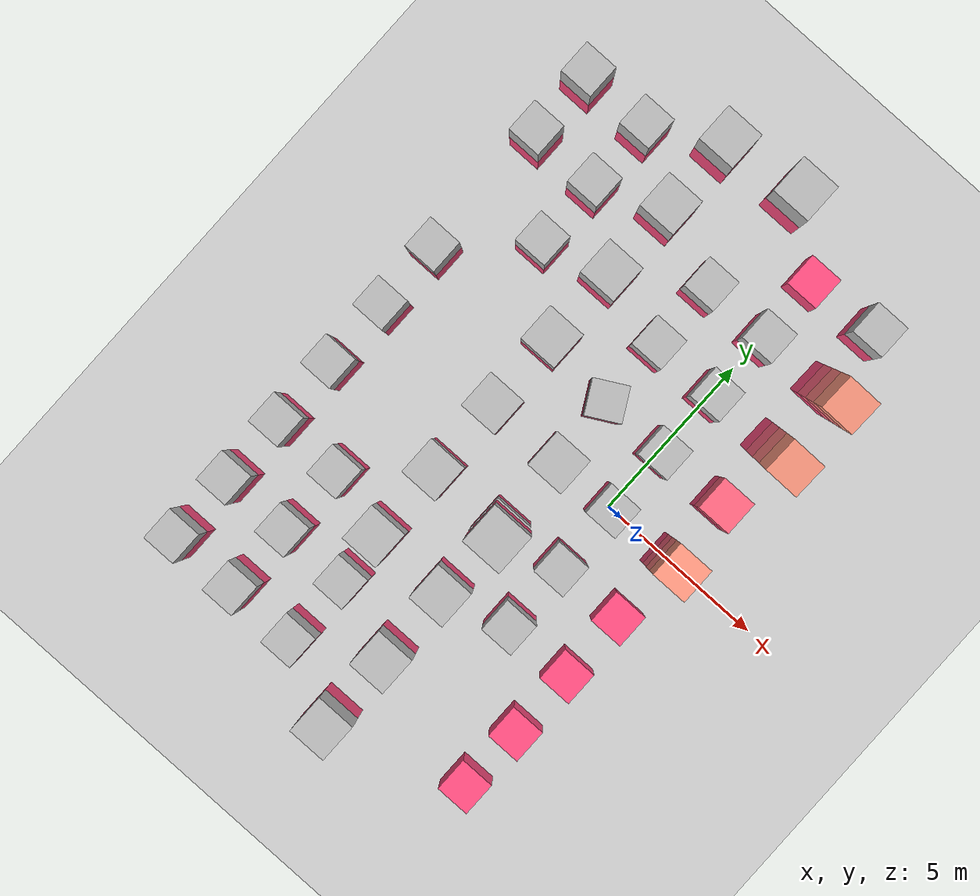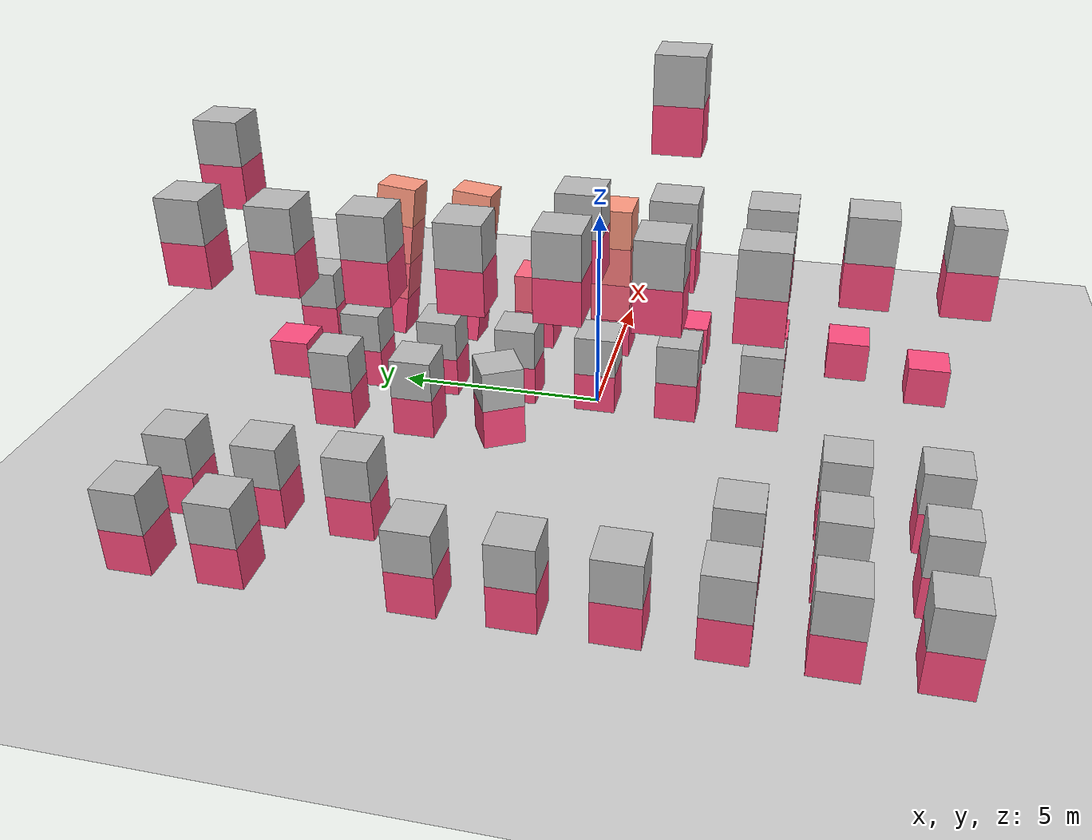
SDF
<?xml version="1.0" ?>
<sdf version="1.7">
    <world name="default">
        <include>
            <uri>model://ground_plane</uri>
        </include>
        <include>
            <uri>model://sun</uri>
        </include>

        <model name="model_test_apply_body_wrench">
            <pose>-8 -8 0.5 0 0 0</pose>
            <static>false</static>
            <link name="link_1">
                <pose>0 0 0 0 0 0</pose>
                <inertial>
                    <inertia>
                        <ixx>0.166</ixx>
                        <ixy>0</ixy>
                        <ixz>0</ixz>
                        <iyy>0.166</iyy>
                        <iyz>0</iyz>
                        <izz>0.166</izz>
                    </inertia>
                    <mass>1.0</mass>
                </inertial>

                <collision name="collision">
                    <pose>0 0 0 0 0 0</pose>
                    <geometry>
                        <box>
                            <size>1 1 1</size>
                        </box>
                    </geometry>
                </collision>

                <visual name="visual">
                    <pose>0 0 0 0 0 0</pose>
                    <geometry>
                        <box>
                            <size>1 1 1</size>
                        </box>
                    </geometry>
                    <material>
                        <diffuse>1.0 0.3 0.5 1.0</diffuse>
                        <specular>.1 .1 .1 1.0</specular>
                    </material>
                </visual>
            </link>
            <link name="link_2">
                <pose>0 0 1 0 0 0</pose>
                <inertial>
                    <inertia>
                        <ixx>0.166</ixx>
                        <ixy>0</ixy>
                        <ixz>0</ixz>
                        <iyy>0.166</iyy>
                        <iyz>0</iyz>
                        <izz>0.166</izz>
                    </inertia>
                    <mass>1.0</mass>
                </inertial>

                <collision name="collision">
                    <pose>0 0 0 0 0 0</pose>
                    <geometry>
                        <box>
                            <size>1 1 1</size>
                        </box>
                    </geometry>
                </collision>

                <visual name="visual">
                    <pose>0 0 0 0 0 0</pose>
                    <geometry>
                        <box>
                            <size>1 1 1</size>
                        </box>
                    </geometry>
                </visual>
            </link>
            <joint name="joint" type="revolute">
                <parent>link_1</parent>
                <child>link_2</child>
                <pose>0 0 0 0 0 0</pose>
                <axis>
                    <xyz>0 0 1</xyz>
                </axis>
            </joint>
        </model>

        <model name="model_test_apply_body_force">
            <pose>-8 -6 0.5 0 0 0</pose>
            <static>false</static>
            <link name="link_1">
                <pose>0 0 0 0 0 0</pose>
                <inertial>
                    <inertia>
                        <ixx>0.166</ixx>
                        <ixy>0</ixy>
                        <ixz>0</ixz>
                        <iyy>0.166</iyy>
                        <iyz>0</iyz>
                        <izz>0.166</izz>
                    </inertia>
                    <mass>1.0</mass>
                </inertial>

                <collision name="collision">
                    <pose>0 0 0 0 0 0</pose>
                    <geometry>
                        <box>
                            <size>1 1 1</size>
                        </box>
                    </geometry>
                </collision>

                <visual name="visual">
                    <pose>0 0 0 0 0 0</pose>
                    <geometry>
                        <box>
                            <size>1 1 1</size>
                        </box>
                    </geometry>
                    <material>
                        <diffuse>1.0 0.3 0.5 1.0</diffuse>
                        <specular>.1 .1 .1 1.0</specular>
                    </material>
                </visual>
            </link>
            <link name="link_2">
                <pose>0 0 1 0 0 0</pose>
                <inertial>
                    <inertia>
                        <ixx>0.166</ixx>
                        <ixy>0</ixy>
                        <ixz>0</ixz>
                        <iyy>0.166</iyy>
                        <iyz>0</iyz>
                        <izz>0.166</izz>
                    </inertia>
                    <mass>1.0</mass>
                </inertial>

                <collision name="collision">
                    <pose>0 0 0 0 0 0</pose>
                    <geometry>
                        <box>
                            <size>1 1 1</size>
                        </box>
                    </geometry>
                </collision>

                <visual name="visual">
                    <pose>0 0 0 0 0 0</pose>
                    <geometry>
                        <box>
                            <size>1 1 1</size>
                        </box>
                    </geometry>
                </visual>
            </link>
            <joint name="joint" type="revolute">
                <parent>link_1</parent>
                <child>link_2</child>
                <pose>0 0 0 0 0 0</pose>
                <axis>
                    <xyz>0 0 1</xyz>
                </axis>
            </joint>
        </model>

        <model name="model_test_apply_body_torque">
            <pose>-8 -4 0.5 0 0 0</pose>
            <static>false</static>
            <link name="link_1">
                <pose>0 0 0 0 0 0</pose>
                <inertial>
                    <inertia>
                        <ixx>0.166</ixx>
                        <ixy>0</ixy>
                        <ixz>0</ixz>
                        <iyy>0.166</iyy>
                        <iyz>0</iyz>
                        <izz>0.166</izz>
                    </inertia>
                    <mass>1.0</mass>
                </inertial>

                <collision name="collision">
                    <pose>0 0 0 0 0 0</pose>
                    <geometry>
                        <box>
                            <size>1 1 1</size>
                        </box>
                    </geometry>
                </collision>

                <visual name="visual">
                    <pose>0 0 0 0 0 0</pose>
                    <geometry>
                        <box>
                            <size>1 1 1</size>
                        </box>
                    </geometry>
                    <material>
                        <diffuse>1.0 0.3 0.5 1.0</diffuse>
                        <specular>.1 .1 .1 1.0</specular>
                    </material>
                </visual>
            </link>
            <link name="link_2">
                <pose>0 0 1 0 0 0</pose>
                <inertial>
                    <inertia>
                        <ixx>0.166</ixx>
                        <ixy>0</ixy>
                        <ixz>0</ixz>
                        <iyy>0.166</iyy>
                        <iyz>0</iyz>
                        <izz>0.166</izz>
                    </inertia>
                    <mass>1.0</mass>
                </inertial>

                <collision name="collision">
                    <pose>0 0 0 0 0 0</pose>
                    <geometry>
                        <box>
                            <size>1 1 1</size>
                        </box>
                    </geometry>
                </collision>

                <visual name="visual">
                    <pose>0 0 0 0 0 0</pose>
                    <geometry>
                        <box>
                            <size>1 1 1</size>
                        </box>
                    </geometry>
                </visual>
            </link>
            <joint name="joint" type="revolute">
                <parent>link_1</parent>
                <child>link_2</child>
                <pose>0 0 0 0 0 0</pose>
                <axis>
                    <xyz>0 0 1</xyz>
                </axis>
            </joint>
        </model>

        <model name="model_test_apply_joint_effort">
            <pose>-8 -2 0.5 0 0 0</pose>
            <static>false</static>
            <link name="link_1">
                <pose>0 0 0 0 0 0</pose>
                <inertial>
                    <inertia>
                        <ixx>0.166</ixx>
                        <ixy>0</ixy>
                        <ixz>0</ixz>
                        <iyy>0.166</iyy>
                        <iyz>0</iyz>
                        <izz>0.166</izz>
                    </inertia>
                    <mass>1.0</mass>
                </inertial>

                <collision name="collision">
                    <pose>0 0 0 0 0 0</pose>
                    <geometry>
                        <box>
                            <size>1 1 1</size>
                        </box>
                    </geometry>
                </collision>

                <visual name="visual">
                    <pose>0 0 0 0 0 0</pose>
                    <geometry>
                        <box>
                            <size>1 1 1</size>
                        </box>
                    </geometry>
                    <material>
                        <diffuse>1.0 0.3 0.5 1.0</diffuse>
                        <specular>.1 .1 .1 1.0</specular>
                    </material>
                </visual>
            </link>
            <link name="link_2">
                <pose>0 0 1 0 0 0</pose>
                <inertial>
                    <inertia>
                        <ixx>0.166</ixx>
                        <ixy>0</ixy>
                        <ixz>0</ixz>
                        <iyy>0.166</iyy>
                        <iyz>0</iyz>
                        <izz>0.166</izz>
                    </inertia>
                    <mass>1.0</mass>
                </inertial>

                <collision name="collision">
                    <pose>0 0 0 0 0 0</pose>
                    <geometry>
                        <box>
                            <size>1 1 1</size>
                        </box>
                    </geometry>
                </collision>

                <visual name="visual">
                    <pose>0 0 0 0 0 0</pose>
                    <geometry>
                        <box>
                            <size>1 1 1</size>
                        </box>
                    </geometry>
                </visual>
            </link>
            <joint name="joint" type="revolute">
                <parent>link_1</parent>
                <child>link_2</child>
                <pose>0 0 0 0 0 0</pose>
                <axis>
                    <xyz>0 0 1</xyz>
                </axis>
            </joint>
        </model>

        <model name="model_test_clear_body_wrenches">
            <pose>-8 0 0.5 0 0 0</pose>
            <static>false</static>
            <link name="link_1">
                <pose>0 0 0 0 0 0</pose>
                <inertial>
                    <inertia>
                        <ixx>0.166</ixx>
                        <ixy>0</ixy>
                        <ixz>0</ixz>
                        <iyy>0.166</iyy>
                        <iyz>0</iyz>
                        <izz>0.166</izz>
                    </inertia>
                    <mass>1.0</mass>
                </inertial>

                <collision name="collision">
                    <pose>0 0 0 0 0 0</pose>
                    <geometry>
                        <box>
                            <size>1 1 1</size>
                        </box>
                    </geometry>
                </collision>

                <visual name="visual">
                    <pose>0 0 0 0 0 0</pose>
                    <geometry>
                        <box>
                            <size>1 1 1</size>
                        </box>
                    </geometry>
                    <material>
                        <diffuse>1.0 0.3 0.5 1.0</diffuse>
                        <specular>.1 .1 .1 1.0</specular>
                    </material>
                </visual>
            </link>
            <link name="link_2">
                <pose>0 0 1 0 0 0</pose>
                <inertial>
                    <inertia>
                        <ixx>0.166</ixx>
                        <ixy>0</ixy>
                        <ixz>0</ixz>
                        <iyy>0.166</iyy>
                        <iyz>0</iyz>
                        <izz>0.166</izz>
                    </inertia>
                    <mass>1.0</mass>
                </inertial>

                <collision name="collision">
                    <pose>0 0 0 0 0 0</pose>
                    <geometry>
                        <box>
                            <size>1 1 1</size>
                        </box>
                    </geometry>
                </collision>

                <visual name="visual">
                    <pose>0 0 0 0 0 0</pose>
                    <geometry>
                        <box>
                            <size>1 1 1</size>
                        </box>
                    </geometry>
                </visual>
            </link>
            <joint name="joint" type="revolute">
                <parent>link_1</parent>
                <child>link_2</child>
                <pose>0 0 0 0 0 0</pose>
                <axis>
                    <xyz>0 0 1</xyz>
                </axis>
            </joint>
        </model>

        <model name="model_test_clear_joint_forces">
            <pose>-8 2 0.5 0 0 0</pose>
            <static>false</static>
            <link name="link_1">
                <pose>0 0 0 0 0 0</pose>
                <inertial>
                    <inertia>
                        <ixx>0.166</ixx>
                        <ixy>0</ixy>
                        <ixz>0</ixz>
                        <iyy>0.166</iyy>
                        <iyz>0</iyz>
                        <izz>0.166</izz>
                    </inertia>
                    <mass>1.0</mass>
                </inertial>

                <collision name="collision">
                    <pose>0 0 0 0 0 0</pose>
                    <geometry>
                        <box>
                            <size>1 1 1</size>
                        </box>
                    </geometry>
                </collision>

                <visual name="visual">
                    <pose>0 0 0 0 0 0</pose>
                    <geometry>
                        <box>
                            <size>1 1 1</size>
                        </box>
                    </geometry>
                    <material>
                        <diffuse>1.0 0.3 0.5 1.0</diffuse>
                        <specular>.1 .1 .1 1.0</specular>
                    </material>
                </visual>
            </link>
            <link name="link_2">
                <pose>0 0 1 0 0 0</pose>
                <inertial>
                    <inertia>
                        <ixx>0.166</ixx>
                        <ixy>0</ixy>
                        <ixz>0</ixz>
                        <iyy>0.166</iyy>
                        <iyz>0</iyz>
                        <izz>0.166</izz>
                    </inertia>
                    <mass>1.0</mass>
                </inertial>

                <collision name="collision">
                    <pose>0 0 0 0 0 0</pose>
                    <geometry>
                        <box>
                            <size>1 1 1</size>
                        </box>
                    </geometry>
                </collision>

                <visual name="visual">
                    <pose>0 0 0 0 0 0</pose>
                    <geometry>
                        <box>
                            <size>1 1 1</size>
                        </box>
                    </geometry>
                </visual>
            </link>
            <joint name="joint" type="revolute">
                <parent>link_1</parent>
                <child>link_2</child>
                <pose>0 0 0 0 0 0</pose>
                <axis>
                    <xyz>0 0 1</xyz>
                </axis>
            </joint>
        </model>

        <light type="point" name="light_test_delete_light">
            <pose>-8 4 2 0 0 -1</pose>
            <diffuse>1 0.1 0.1 1</diffuse>
            <specular>.1 .1 .1 1</specular>
            <attenuation>
                <range>20</range>
                <constant>0.8</constant>
                <linear>0.2</linear>
                <quadratic>0.01</quadratic>
            </attenuation>
            <cast_shadows>false</cast_shadows>
        </light>

        <model name="model_test_delete_model">
            <pose>-8 6 0.5 0 0 0</pose>
            <static>false</static>
            <link name="link_1">
                <pose>0 0 0 0 0 0</pose>
                <inertial>
                    <inertia>
                        <ixx>0.166</ixx>
                        <ixy>0</ixy>
                        <ixz>0</ixz>
                        <iyy>0.166</iyy>
                        <iyz>0</iyz>
                        <izz>0.166</izz>
                    </inertia>
                    <mass>1.0</mass>
                </inertial>

                <collision name="collision">
                    <pose>0 0 0 0 0 0</pose>
                    <geometry>
                        <box>
                            <size>1 1 1</size>
                        </box>
                    </geometry>
                </collision>

                <visual name="visual">
                    <pose>0 0 0 0 0 0</pose>
                    <geometry>
                        <box>
                            <size>1 1 1</size>
                        </box>
                    </geometry>
                    <material>
                        <diffuse>1.0 0.3 0.5 1.0</diffuse>
                        <specular>.1 .1 .1 1.0</specular>
                    </material>
                </visual>
            </link>
            <link name="link_2">
                <pose>0 0 1 0 0 0</pose>
                <inertial>
                    <inertia>
                        <ixx>0.166</ixx>
                        <ixy>0</ixy>
                        <ixz>0</ixz>
                        <iyy>0.166</iyy>
                        <iyz>0</iyz>
                        <izz>0.166</izz>
                    </inertia>
                    <mass>1.0</mass>
                </inertial>

                <collision name="collision">
                    <pose>0 0 0 0 0 0</pose>
                    <geometry>
                        <box>
                            <size>1 1 1</size>
                        </box>
                    </geometry>
                </collision>

                <visual name="visual">
                    <pose>0 0 0 0 0 0</pose>
                    <geometry>
                        <box>
                            <size>1 1 1</size>
                        </box>
                    </geometry>
                </visual>
            </link>
            <joint name="joint" type="revolute">
                <parent>link_1</parent>
                <child>link_2</child>
                <pose>0 0 0 0 0 0</pose>
                <axis>
                    <xyz>0 0 1</xyz>
                </axis>
            </joint>
        </model>

        <model name="model_test_get_joint_properties">
            <pose>-8 8 0.5 0 0 0</pose>
            <static>false</static>
            <link name="link_1">
                <pose>0 0 0 0 0 0</pose>
                <inertial>
                    <inertia>
                        <ixx>0.166</ixx>
                        <ixy>0</ixy>
                        <ixz>0</ixz>
                        <iyy>0.166</iyy>
                        <iyz>0</iyz>
                        <izz>0.166</izz>
                    </inertia>
                    <mass>1.0</mass>
                </inertial>

                <collision name="collision">
                    <pose>0 0 0 0 0 0</pose>
                    <geometry>
                        <box>
                            <size>1 1 1</size>
                        </box>
                    </geometry>
                </collision>

                <visual name="visual">
                    <pose>0 0 0 0 0 0</pose>
                    <geometry>
                        <box>
                            <size>1 1 1</size>
                        </box>
                    </geometry>
                    <material>
                        <diffuse>1.0 0.3 0.5 1.0</diffuse>
                        <specular>.1 .1 .1 1.0</specular>
                    </material>
                </visual>
            </link>
            <link name="link_2">
                <pose>0 0 1 0 0 0</pose>
                <inertial>
                    <inertia>
                        <ixx>0.166</ixx>
                        <ixy>0</ixy>
                        <ixz>0</ixz>
                        <iyy>0.166</iyy>
                        <iyz>0</iyz>
                        <izz>0.166</izz>
                    </inertia>
                    <mass>1.0</mass>
                </inertial>

                <collision name="collision">
                    <pose>0 0 0 0 0 0</pose>
                    <geometry>
                        <box>
                            <size>1 1 1</size>
                        </box>
                    </geometry>
                </collision>

                <visual name="visual">
                    <pose>0 0 0 0 0 0</pose>
                    <geometry>
                        <box>
                            <size>1 1 1</size>
                        </box>
                    </geometry>
                </visual>
            </link>
            <joint name="joint" type="revolute">
                <parent>link_1</parent>
                <child>link_2</child>
                <pose>0 0 0 0 0 0</pose>
                <axis>
                    <xyz>0 0 1</xyz>
                </axis>
            </joint>
        </model>

        <model name="model_test_get_joint_type">
            <pose>-6 -8 0.5 0 0 0</pose>
            <static>false</static>
            <link name="link_1">
                <pose>0 0 0 0 0 0</pose>
                <inertial>
                    <inertia>
                        <ixx>0.166</ixx>
                        <ixy>0</ixy>
                        <ixz>0</ixz>
                        <iyy>0.166</iyy>
                        <iyz>0</iyz>
                        <izz>0.166</izz>
                    </inertia>
                    <mass>1.0</mass>
                </inertial>

                <collision name="collision">
                    <pose>0 0 0 0 0 0</pose>
                    <geometry>
                        <box>
                            <size>1 1 1</size>
                        </box>
                    </geometry>
                </collision>

                <visual name="visual">
                    <pose>0 0 0 0 0 0</pose>
                    <geometry>
                        <box>
                            <size>1 1 1</size>
                        </box>
                    </geometry>
                    <material>
                        <diffuse>1.0 0.3 0.5 1.0</diffuse>
                        <specular>.1 .1 .1 1.0</specular>
                    </material>
                </visual>
            </link>
            <link name="link_2">
                <pose>0 0 1 0 0 0</pose>
                <inertial>
                    <inertia>
                        <ixx>0.166</ixx>
                        <ixy>0</ixy>
                        <ixz>0</ixz>
                        <iyy>0.166</iyy>
                        <iyz>0</iyz>
                        <izz>0.166</izz>
                    </inertia>
                    <mass>1.0</mass>
                </inertial>

                <collision name="collision">
                    <pose>0 0 0 0 0 0</pose>
                    <geometry>
                        <box>
                            <size>1 1 1</size>
                        </box>
                    </geometry>
                </collision>

                <visual name="visual">
                    <pose>0 0 0 0 0 0</pose>
                    <geometry>
                        <box>
                            <size>1 1 1</size>
                        </box>
                    </geometry>
                </visual>
            </link>
            <joint name="joint" type="revolute">
                <parent>link_1</parent>
                <child>link_2</child>
                <pose>0 0 0 0 0 0</pose>
                <axis>
                    <xyz>0 0 1</xyz>
                </axis>
            </joint>
        </model>

        <model name="model_test_get_joint_position">
            <pose>-6 -6 0.5 0 0 0</pose>
            <static>false</static>
            <link name="link_1">
                <pose>0 0 0 0 0 0</pose>
                <inertial>
                    <inertia>
                        <ixx>0.166</ixx>
                        <ixy>0</ixy>
                        <ixz>0</ixz>
                        <iyy>0.166</iyy>
                        <iyz>0</iyz>
                        <izz>0.166</izz>
                    </inertia>
                    <mass>1.0</mass>
                </inertial>

                <collision name="collision">
                    <pose>0 0 0 0 0 0</pose>
                    <geometry>
                        <box>
                            <size>1 1 1</size>
                        </box>
                    </geometry>
                </collision>

                <visual name="visual">
                    <pose>0 0 0 0 0 0</pose>
                    <geometry>
                        <box>
                            <size>1 1 1</size>
                        </box>
                    </geometry>
                    <material>
                        <diffuse>1.0 0.3 0.5 1.0</diffuse>
                        <specular>.1 .1 .1 1.0</specular>
                    </material>
                </visual>
            </link>
            <link name="link_2">
                <pose>0 0 1 0 0 0</pose>
                <inertial>
                    <inertia>
                        <ixx>0.166</ixx>
                        <ixy>0</ixy>
                        <ixz>0</ixz>
                        <iyy>0.166</iyy>
                        <iyz>0</iyz>
                        <izz>0.166</izz>
                    </inertia>
                    <mass>1.0</mass>
                </inertial>

                <collision name="collision">
                    <pose>0 0 0 0 0 0</pose>
                    <geometry>
                        <box>
                            <size>1 1 1</size>
                        </box>
                    </geometry>
                </collision>

                <visual name="visual">
                    <pose>0 0 0 0 0 0</pose>
                    <geometry>
                        <box>
                            <size>1 1 1</size>
                        </box>
                    </geometry>
                </visual>
            </link>
            <joint name="joint" type="revolute">
                <parent>link_1</parent>
                <child>link_2</child>
                <pose>0 0 0 0 0 0</pose>
                <axis>
                    <xyz>0 0 1</xyz>
                </axis>
            </joint>
        </model>

        <model name="model_test_get_joint_rate">
            <pose>-6 -4 0.5 0 0 0</pose>
            <static>false</static>
            <link name="link_1">
                <pose>0 0 0 0 0 0</pose>
                <inertial>
                    <inertia>
                        <ixx>0.166</ixx>
                        <ixy>0</ixy>
                        <ixz>0</ixz>
                        <iyy>0.166</iyy>
                        <iyz>0</iyz>
                        <izz>0.166</izz>
                    </inertia>
                    <mass>1.0</mass>
                </inertial>

                <collision name="collision">
                    <pose>0 0 0 0 0 0</pose>
                    <geometry>
                        <box>
                            <size>1 1 1</size>
                        </box>
                    </geometry>
                </collision>

                <visual name="visual">
                    <pose>0 0 0 0 0 0</pose>
                    <geometry>
                        <box>
                            <size>1 1 1</size>
                        </box>
                    </geometry>
                    <material>
                        <diffuse>1.0 0.3 0.5 1.0</diffuse>
                        <specular>.1 .1 .1 1.0</specular>
                    </material>
                </visual>
            </link>
            <link name="link_2">
                <pose>0 0 1 0 0 0</pose>
                <inertial>
                    <inertia>
                        <ixx>0.166</ixx>
                        <ixy>0</ixy>
                        <ixz>0</ixz>
                        <iyy>0.166</iyy>
                        <iyz>0</iyz>
                        <izz>0.166</izz>
                    </inertia>
                    <mass>1.0</mass>
                </inertial>

                <collision name="collision">
                    <pose>0 0 0 0 0 0</pose>
                    <geometry>
                        <box>
                            <size>1 1 1</size>
                        </box>
                    </geometry>
                </collision>

                <visual name="visual">
                    <pose>0 0 0 0 0 0</pose>
                    <geometry>
                        <box>
                            <size>1 1 1</size>
                        </box>
                    </geometry>
                </visual>
            </link>
            <joint name="joint" type="revolute">
                <parent>link_1</parent>
                <child>link_2</child>
                <pose>0 0 0 0 0 0</pose>
                <axis>
                    <xyz>0 0 1</xyz>
                </axis>
            </joint>
        </model>

        <light type="point" name="light_test_get_light_properties">
            <pose>-6 -2 2 0 0 -1</pose>
            <diffuse>0.1 0.2 0.3 0.4</diffuse>
            <specular>.1 .1 .1 1</specular>
            <attenuation>
                <range>20</range>
                <constant>0.5</constant>
                <linear>0.6</linear>
                <quadratic>0.7</quadratic>
            </attenuation>
            <cast_shadows>false</cast_shadows>
        </light>

        <light type="point" name="light_test_get_light_color">
            <pose>-6 0 2 0 0 -1</pose>
            <diffuse>0.2 0.3 0.4 0.5</diffuse>
            <specular>.1 .1 .1 1</specular>
            <attenuation>
                <range>20</range>
                <constant>0.8</constant>
                <linear>0.2</linear>
                <quadratic>0.01</quadratic>
            </attenuation>
            <cast_shadows>false</cast_shadows>
        </light>

        <light type="point" name="light_test_get_light_attenuation">
            <pose>-6 2 2 0 0 -1</pose>
            <diffuse>0.2 0.3 0.4 0.5</diffuse>
            <specular>.1 .1 .1 1</specular>
            <attenuation>
                <range>20</range>
                <constant>0.4</constant>
                <linear>0.5</linear>
                <quadratic>0.6</quadratic>
            </attenuation>
            <cast_shadows>false</cast_shadows>
        </light>

        <model name="model_test_get_link_properties">
            <pose>-6 4 0.5 0 0 0</pose>
            <static>false</static>
            <link name="link_1">
                <pose>0 0 0 0 0 0</pose>
                <inertial>
                    <inertia>
                        <ixx>0.166</ixx>
                        <ixy>0</ixy>
                        <ixz>0</ixz>
                        <iyy>0.166</iyy>
                        <iyz>0</iyz>
                        <izz>0.166</izz>
                    </inertia>
                    <mass>1.0</mass>
                </inertial>

                <collision name="collision">
                    <pose>0 0 0 0 0 0</pose>
                    <geometry>
                        <box>
                            <size>1 1 1</size>
                        </box>
                    </geometry>
                </collision>

                <visual name="visual">
                    <pose>0 0 0 0 0 0</pose>
                    <geometry>
                        <box>
                            <size>1 1 1</size>
                        </box>
                    </geometry>
                    <material>
                        <diffuse>1.0 0.3 0.5 1.0</diffuse>
                        <specular>.1 .1 .1 1.0</specular>
                    </material>
                </visual>
            </link>
            <link name="link_2">
                <pose>0 0 1 0 0 0</pose>
                <inertial>
                    <inertia>
                        <ixx>0.11</ixx>
                        <ixy>0.03</ixy>
                        <ixz>0.8</ixz>
                        <iyy>0.241</iyy>
                        <iyz>0.001</iyz>
                        <izz>0.23</izz>
                    </inertia>
                    <mass>1.0</mass>
                </inertial>

                <collision name="collision">
                    <pose>0 0 0 0 0 0</pose>
                    <geometry>
                        <box>
                            <size>1 1 1</size>
                        </box>
                    </geometry>
                </collision>

                <visual name="visual">
                    <pose>0 0 0 0 0 0</pose>
                    <geometry>
                        <box>
                            <size>1 1 1</size>
                        </box>
                    </geometry>
                </visual>
            </link>
            <joint name="joint" type="revolute">
                <parent>link_1</parent>
                <child>link_2</child>
                <pose>0 0 0 0 0 0</pose>
                <axis>
                    <xyz>0 0 1</xyz>
                </axis>
            </joint>
        </model>

        <model name="model_test_get_link_gravity_mode">
            <pose>-6 6 0.5 0 0 0</pose>
            <static>false</static>
            <link name="link_1">
                <pose>0 0 0 0 0 0</pose>
                <inertial>
                    <inertia>
                        <ixx>0.166</ixx>
                        <ixy>0</ixy>
                        <ixz>0</ixz>
                        <iyy>0.166</iyy>
                        <iyz>0</iyz>
                        <izz>0.166</izz>
                    </inertia>
                    <mass>1.0</mass>
                </inertial>
                <collision name="collision">
                    <geometry>
                        <box>
                            <size>1 1 1</size>
                        </box>
                    </geometry>
                </collision>
                <visual name="visual">
                    <geometry>
                        <box>
                            <size>1 1 1</size>
                        </box>
                    </geometry>
                    <material>
                        <diffuse>1.0 0.3 0.5 1.0</diffuse>
                        <specular>.1 .1 .1 1.0</specular>
                    </material>
                </visual>
            </link>
            <link name="link_2">
                <pose>0 0 1 0 0 0</pose>
                <gravity>false</gravity>
                <inertial>
                    <inertia>
                        <ixx>0.166</ixx>
                        <ixy>0</ixy>
                        <ixz>0</ixz>
                        <iyy>0.166</iyy>
                        <iyz>0</iyz>
                        <izz>0.166</izz>
                    </inertia>
                    <mass>1.0</mass>
                </inertial>
                <collision name="collision">
                    <geometry>
                        <box>
                            <size>1 1 1</size>
                        </box>
                    </geometry>
                </collision>
                <visual name="visual">
                    <geometry>
                        <box>
                            <size>1 1 1</size>
                        </box>
                    </geometry>
                </visual>
            </link>
            <joint name="joint" type="revolute">
                <parent>link_1</parent>
                <child>link_2</child>
                <pose>0 0 0 0 0 0</pose>
                <axis>
                    <xyz>0 0 1</xyz>
                </axis>
            </joint>
        </model>

        <model name="model_test_get_link_mass">
            <pose>-6 8 0.5 0 0 0</pose>
            <static>false</static>
            <link name="link_1">
                <pose>0 0 0 0 0 0</pose>
                <inertial>
                    <inertia>
                        <ixx>0.166</ixx>
                        <ixy>0</ixy>
                        <ixz>0</ixz>
                        <iyy>0.166</iyy>
                        <iyz>0</iyz>
                        <izz>0.166</izz>
                    </inertia>
                    <mass>1.0</mass>
                </inertial>
                <collision name="collision">
                    <geometry>
                        <box>
                            <size>1 1 1</size>
                        </box>
                    </geometry>
                </collision>
                <visual name="visual">
                    <geometry>
                        <box>
                            <size>1 1 1</size>
                        </box>
                    </geometry>
                    <material>
                        <diffuse>1.0 0.3 0.5 1.0</diffuse>
                        <specular>.1 .1 .1 1.0</specular>
                    </material>
                </visual>
            </link>
            <link name="link_2">
                <pose>0 0 1 0 0 0</pose>
                <inertial>
                    <inertia>
                        <ixx>0.333</ixx>
                        <ixy>0</ixy>
                        <ixz>0</ixz>
                        <iyy>0.333</iyy>
                        <iyz>0</iyz>
                        <izz>0.333</izz>
                    </inertia>
                    <mass>2.0</mass>
                </inertial>
                <collision name="collision">
                    <geometry>
                        <box>
                            <size>1 1 1</size>
                        </box>
                    </geometry>
                </collision>
                <visual name="visual">
                    <geometry>
                        <box>
                            <size>1 1 1</size>
                        </box>
                    </geometry>
                </visual>
            </link>
            <joint name="joint" type="revolute">
                <parent>link_1</parent>
                <child>link_2</child>
                <pose>0 0 0 0 0 0</pose>
                <axis>
                    <xyz>0 0 1</xyz>
                </axis>
            </joint>
        </model>

        <model name="model_test_get_link_moments">
            <pose>-4 -8 0.5 0 0 0</pose>
            <static>false</static>
            <link name="link_1">
                <pose>0 0 0 0 0 0</pose>
                <inertial>
                    <inertia>
                        <ixx>0.16</ixx>
                        <ixy>0.01</ixy>
                        <ixz>0.02</ixz>
                        <iyy>0.17</iyy>
                        <iyz>0.03</iyz>
                        <izz>0.18</izz>
                    </inertia>
                    <mass>1.0</mass>
                </inertial>
                <collision name="collision">
                    <geometry>
                        <box>
                            <size>1 1 1</size>
                        </box>
                    </geometry>
                </collision>
                <visual name="visual">
                    <geometry>
                        <box>
                            <size>1 1 1</size>
                        </box>
                    </geometry>
                    <material>
                        <diffuse>1.0 0.3 0.5 1.0</diffuse>
                        <specular>.1 .1 .1 1.0</specular>
                    </material>
                </visual>
            </link>
            <link name="link_2">
                <pose>0 0 1 0 0 0</pose>
                <inertial>
                    <inertia>
                        <ixx>0.166</ixx>
                        <ixy>0</ixy>
                        <ixz>0</ixz>
                        <iyy>0.166</iyy>
                        <iyz>0</iyz>
                        <izz>0.166</izz>
                    </inertia>
                    <mass>1.0</mass>
                </inertial>
                <collision name="collision">
                    <geometry>
                        <box>
                            <size>1 1 1</size>
                        </box>
                    </geometry>
                </collision>
                <visual name="visual">
                    <geometry>
                        <box>
                            <size>1 1 1</size>
                        </box>
                    </geometry>
                </visual>
            </link>
            <joint name="joint" type="revolute">
                <parent>link_1</parent>
                <child>link_2</child>
                <pose>0 0 0 0 0 0</pose>
                <axis>
                    <xyz>0 0 1</xyz>
                </axis>
            </joint>
        </model>

        <model name="model_test_get_link_state">
            <pose>-4 -6 0.5 0 0 0</pose>
            <static>false</static>
            <link name="link_1">
                <pose>0 0 0 0 0 0</pose>
                <inertial>
                    <inertia>
                        <ixx>0.166</ixx>
                        <ixy>0</ixy>
                        <ixz>0</ixz>
                        <iyy>0.166</iyy>
                        <iyz>0</iyz>
                        <izz>0.166</izz>
                    </inertia>
                    <mass>1.0</mass>
                </inertial>

                <collision name="collision">
                    <pose>0 0 0 0 0 0</pose>
                    <geometry>
                        <box>
                            <size>1 1 1</size>
                        </box>
                    </geometry>
                </collision>

                <visual name="visual">
                    <pose>0 0 0 0 0 0</pose>
                    <geometry>
                        <box>
                            <size>1 1 1</size>
                        </box>
                    </geometry>
                    <material>
                        <diffuse>1.0 0.3 0.5 1.0</diffuse>
                        <specular>.1 .1 .1 1.0</specular>
                    </material>
                </visual>
            </link>
            <link name="link_2">
                <pose>0 0 1 0 0 0</pose>
                <inertial>
                    <inertia>
                        <ixx>0.11</ixx>
                        <ixy>0.03</ixy>
                        <ixz>0.8</ixz>
                        <iyy>0.241</iyy>
                        <iyz>0.001</iyz>
                        <izz>0.23</izz>
                    </inertia>
                    <mass>1.0</mass>
                </inertial>

                <collision name="collision">
                    <pose>0 0 0 0 0 0</pose>
                    <geometry>
                        <box>
                            <size>1 1 1</size>
                        </box>
                    </geometry>
                </collision>

                <visual name="visual">
                    <pose>0 0 0 0 0 0</pose>
                    <geometry>
                        <box>
                            <size>1 1 1</size>
                        </box>
                    </geometry>
                </visual>
            </link>
            <joint name="joint" type="revolute">
                <parent>link_1</parent>
                <child>link_2</child>
                <pose>0 0 0 0 0 0</pose>
                <axis>
                    <xyz>0 0 1</xyz>
                </axis>
            </joint>
        </model>

        <model name="model_test_get_link_position">
            <pose>-4 -4 5 0 0 0</pose>
            <static>false</static>
            <link name="link_1">
                <pose>0 0 0 0 0 0</pose>
                <inertial>
                    <inertia>
                        <ixx>0.166</ixx>
                        <ixy>0</ixy>
                        <ixz>0</ixz>
                        <iyy>0.166</iyy>
                        <iyz>0</iyz>
                        <izz>0.166</izz>
                    </inertia>
                    <mass>1.0</mass>
                </inertial>

                <collision name="collision">
                    <pose>0 0 0 0 0 0</pose>
                    <geometry>
                        <box>
                            <size>1 1 1</size>
                        </box>
                    </geometry>
                </collision>

                <visual name="visual">
                    <pose>0 0 0 0 0 0</pose>
                    <geometry>
                        <box>
                            <size>1 1 1</size>
                        </box>
                    </geometry>
                    <material>
                        <diffuse>1.0 0.3 0.5 1.0</diffuse>
                        <specular>.1 .1 .1 1.0</specular>
                    </material>
                </visual>
            </link>
            <link name="link_2">
                <pose>0 0 1 0 0 0</pose>
                <inertial>
                    <inertia>
                        <ixx>0.11</ixx>
                        <ixy>0.03</ixy>
                        <ixz>0.8</ixz>
                        <iyy>0.241</iyy>
                        <iyz>0.001</iyz>
                        <izz>0.23</izz>
                    </inertia>
                    <mass>1.0</mass>
                </inertial>

                <collision name="collision">
                    <pose>0 0 0 0 0 0</pose>
                    <geometry>
                        <box>
                            <size>1 1 1</size>
                        </box>
                    </geometry>
                </collision>

                <visual name="visual">
                    <pose>0 0 0 0 0 0</pose>
                    <geometry>
                        <box>
                            <size>1 1 1</size>
                        </box>
                    </geometry>
                </visual>
            </link>
            <joint name="joint" type="revolute">
                <parent>link_1</parent>
                <child>link_2</child>
                <pose>0 0 0 0 0 0</pose>
                <axis>
                    <xyz>0 0 1</xyz>
                </axis>
            </joint>
        </model>

        <model name="model_test_get_link_orientation">
            <pose>-4 -2 5 0 0 0</pose>
            <static>false</static>
            <link name="link_1">
                <pose>0 0 0 0 0 0</pose>
                <inertial>
                    <inertia>
                        <ixx>0.166</ixx>
                        <ixy>0</ixy>
                        <ixz>0</ixz>
                        <iyy>0.166</iyy>
                        <iyz>0</iyz>
                        <izz>0.166</izz>
                    </inertia>
                    <mass>1.0</mass>
                </inertial>

                <collision name="collision">
                    <pose>0 0 0 0 0 0</pose>
                    <geometry>
                        <box>
                            <size>1 1 1</size>
                        </box>
                    </geometry>
                </collision>

                <visual name="visual">
                    <pose>0 0 0 0 0 0</pose>
                    <geometry>
                        <box>
                            <size>1 1 1</size>
                        </box>
                    </geometry>
                    <material>
                        <diffuse>1.0 0.3 0.5 1.0</diffuse>
                        <specular>.1 .1 .1 1.0</specular>
                    </material>
                </visual>
            </link>
            <link name="link_2">
                <pose>0 0 1 0 0 0</pose>
                <inertial>
                    <inertia>
                        <ixx>0.11</ixx>
                        <ixy>0.03</ixy>
                        <ixz>0.8</ixz>
                        <iyy>0.241</iyy>
                        <iyz>0.001</iyz>
                        <izz>0.23</izz>
                    </inertia>
                    <mass>1.0</mass>
                </inertial>

                <collision name="collision">
                    <pose>0 0 0 0 0 0</pose>
                    <geometry>
                        <box>
                            <size>1 1 1</size>
                        </box>
                    </geometry>
                </collision>

                <visual name="visual">
                    <pose>0 0 0 0 0 0</pose>
                    <geometry>
                        <box>
                            <size>1 1 1</size>
                        </box>
                    </geometry>
                </visual>
            </link>
            <joint name="joint" type="revolute">
                <parent>link_1</parent>
                <child>link_2</child>
                <pose>0 0 0 0 0 0</pose>
                <axis>
                    <xyz>0 0 1</xyz>
                </axis>
            </joint>
        </model>

        <model name="model_test_get_link_linear_velocity">
            <pose>-4 0 5 0 0 0</pose>
            <static>false</static>
            <link name="link_1">
                <pose>0 0 0 0 0 0</pose>
                <inertial>
                    <inertia>
                        <ixx>0.166</ixx>
                        <ixy>0</ixy>
                        <ixz>0</ixz>
                        <iyy>0.166</iyy>
                        <iyz>0</iyz>
                        <izz>0.166</izz>
                    </inertia>
                    <mass>1.0</mass>
                </inertial>

                <collision name="collision">
                    <pose>0 0 0 0 0 0</pose>
                    <geometry>
                        <box>
                            <size>1 1 1</size>
                        </box>
                    </geometry>
                </collision>

                <visual name="visual">
                    <pose>0 0 0 0 0 0</pose>
                    <geometry>
                        <box>
                            <size>1 1 1</size>
                        </box>
                    </geometry>
                    <material>
                        <diffuse>1.0 0.3 0.5 1.0</diffuse>
                        <specular>.1 .1 .1 1.0</specular>
                    </material>
                </visual>
            </link>
            <link name="link_2">
                <pose>0 0 1 0 0 0</pose>
                <inertial>
                    <inertia>
                        <ixx>0.11</ixx>
                        <ixy>0.03</ixy>
                        <ixz>0.8</ixz>
                        <iyy>0.241</iyy>
                        <iyz>0.001</iyz>
                        <izz>0.23</izz>
                    </inertia>
                    <mass>1.0</mass>
                </inertial>

                <collision name="collision">
                    <pose>0 0 0 0 0 0</pose>
                    <geometry>
                        <box>
                            <size>1 1 1</size>
                        </box>
                    </geometry>
                </collision>

                <visual name="visual">
                    <pose>0 0 0 0 0 0</pose>
                    <geometry>
                        <box>
                            <size>1 1 1</size>
                        </box>
                    </geometry>
                </visual>
            </link>
            <joint name="joint" type="revolute">
                <parent>link_1</parent>
                <child>link_2</child>
                <pose>0 0 0 0 0 0</pose>
                <axis>
                    <xyz>0 0 1</xyz>
                </axis>
            </joint>
        </model>

        <model name="model_test_get_link_angular_velocity">
            <pose>-4 2 5 0 0 0</pose>
            <static>false</static>
            <link name="link_1">
                <pose>0 0 0 0 0 0</pose>
                <inertial>
                    <inertia>
                        <ixx>0.166</ixx>
                        <ixy>0</ixy>
                        <ixz>0</ixz>
                        <iyy>0.166</iyy>
                        <iyz>0</iyz>
                        <izz>0.166</izz>
                    </inertia>
                    <mass>1.0</mass>
                </inertial>

                <collision name="collision">
                    <pose>0 0 0 0 0 0</pose>
                    <geometry>
                        <box>
                            <size>1 1 1</size>
                        </box>
                    </geometry>
                </collision>

                <visual name="visual">
                    <pose>0 0 0 0 0 0</pose>
                    <geometry>
                        <box>
                            <size>1 1 1</size>
                        </box>
                    </geometry>
                    <material>
                        <diffuse>1.0 0.3 0.5 1.0</diffuse>
                        <specular>.1 .1 .1 1.0</specular>
                    </material>
                </visual>
            </link>
            <link name="link_2">
                <pose>0 0 1 0 0 0</pose>
                <inertial>
                    <inertia>
                        <ixx>0.166</ixx>
                        <ixy>0</ixy>
                        <ixz>0</ixz>
                        <iyy>0.166</iyy>
                        <iyz>0</iyz>
                        <izz>0.166</izz>
                    </inertia>
                    <mass>1.0</mass>
                </inertial>

                <collision name="collision">
                    <pose>0 0 0 0 0 0</pose>
                    <geometry>
                        <box>
                            <size>1 1 1</size>
                        </box>
                    </geometry>
                </collision>

                <visual name="visual">
                    <pose>0 0 0 0 0 0</pose>
                    <geometry>
                        <box>
                            <size>1 1 1</size>
                        </box>
                    </geometry>
                </visual>
            </link>
            <joint name="joint" type="revolute">
                <parent>link_1</parent>
                <child>link_2</child>
                <pose>0 0 0 0 0 0</pose>
                <axis>
                    <xyz>0 0 1</xyz>
                </axis>
            </joint>
        </model>

        <model name="model_test_get_model_properties">
            <pose>-4 4 5 0 0 0</pose>
            <static>false</static>
            <link name="link_1">
                <pose>0 0 0 0 0 0</pose>
                <inertial>
                    <inertia>
                        <ixx>0.166</ixx>
                        <ixy>0</ixy>
                        <ixz>0</ixz>
                        <iyy>0.166</iyy>
                        <iyz>0</iyz>
                        <izz>0.166</izz>
                    </inertia>
                    <mass>1.0</mass>
                </inertial>
                <collision name="col_link_1">
                    <geometry>
                        <box>
                            <size>1 1 1</size>
                        </box>
                    </geometry>
                </collision>
                <visual name="visual">
                    <geometry>
                        <box>
                            <size>1 1 1</size>
                        </box>
                    </geometry>
                    <material>
                        <diffuse>1.0 0.3 0.5 1.0</diffuse>
                        <specular>.1 .1 .1 1.0</specular>
                    </material>
                </visual>
            </link>
            <link name="link_2">
                <pose>0 0 1 0 0 0</pose>
                <inertial>
                    <inertia>
                        <ixx>0.166</ixx>
                        <ixy>0</ixy>
                        <ixz>0</ixz>
                        <iyy>0.166</iyy>
                        <iyz>0</iyz>
                        <izz>0.166</izz>
                    </inertia>
                    <mass>1.0</mass>
                </inertial>
                <collision name="col_link_2">
                    <geometry>
                        <box>
                            <size>1 1 1</size>
                        </box>
                    </geometry>
                </collision>
                <visual name="visual">
                    <geometry>
                        <box>
                            <size>1 1 1</size>
                        </box>
                    </geometry>
                </visual>
            </link>
            <joint name="my_joint" type="revolute">
                <parent>link_1</parent>
                <child>link_2</child>
                <pose>0 0 0 0 0 0</pose>
                <axis>
                    <xyz>0 0 1</xyz>
                </axis>
            </joint>
        </model>

        <model name="model_test_get_parent_model_name_parent">
            <pose>-4 6 5 0 0 0</pose>
            <model name="model_test_get_parent_model_name">
                <static>false</static>
                <link name="link_1">
                    <pose>0 0 0 0 0 0</pose>
                    <inertial>
                        <inertia>
                            <ixx>0.166</ixx>
                            <ixy>0</ixy>
                            <ixz>0</ixz>
                            <iyy>0.166</iyy>
                            <iyz>0</iyz>
                            <izz>0.166</izz>
                        </inertia>
                        <mass>1.0</mass>
                    </inertial>
                    <collision name="collision">
                        <geometry>
                            <box>
                                <size>1 1 1</size>
                            </box>
                        </geometry>
                    </collision>
                    <visual name="visual">
                        <geometry>
                            <box>
                                <size>1 1 1</size>
                            </box>
                        </geometry>
                        <material>
                            <diffuse>1.0 0.3 0.5 1.0</diffuse>
                            <specular>.1 .1 .1 1.0</specular>
                        </material>
                    </visual>
                </link>
                <link name="link_2">
                    <pose>0 0 1 0 0 0</pose>
                    <inertial>
                        <inertia>
                            <ixx>0.166</ixx>
                            <ixy>0</ixy>
                            <ixz>0</ixz>
                            <iyy>0.166</iyy>
                            <iyz>0</iyz>
                            <izz>0.166</izz>
                        </inertia>
                        <mass>1.0</mass>
                    </inertial>
                    <collision name="collision">
                        <geometry>
                            <box>
                                <size>1 1 1</size>
                            </box>
                        </geometry>
                    </collision>
                    <visual name="visual">
                        <geometry>
                            <box>
                                <size>1 1 1</size>
                            </box>
                        </geometry>
                    </visual>
                </link>
                <joint name="joint" type="revolute">
                    <parent>link_1</parent>
                    <child>link_2</child>
                    <pose>0 0 0 0 0 0</pose>
                    <axis>
                        <xyz>0 0 1</xyz>
                    </axis>
                </joint>
            </model>
        </model>

        <model name="model_test_get_canonical_link_name">
            <pose>-4 8 5 0 0 0</pose>
            <static>false</static>
            <link name="link_1">
                <pose>0 0 0 0 0 0</pose>
                <inertial>
                    <inertia>
                        <ixx>0.166</ixx>
                        <ixy>0</ixy>
                        <ixz>0</ixz>
                        <iyy>0.166</iyy>
                        <iyz>0</iyz>
                        <izz>0.166</izz>
                    </inertia>
                    <mass>1.0</mass>
                </inertial>
                <collision name="collision">
                    <geometry>
                        <box>
                            <size>1 1 1</size>
                        </box>
                    </geometry>
                </collision>
                <visual name="visual">
                    <geometry>
                        <box>
                            <size>1 1 1</size>
                        </box>
                    </geometry>
                    <material>
                        <diffuse>1.0 0.3 0.5 1.0</diffuse>
                        <specular>.1 .1 .1 1.0</specular>
                    </material>
                </visual>
            </link>
            <link name="link_2">
                <pose>0 0 1 0 0 0</pose>
                <inertial>
                    <inertia>
                        <ixx>0.166</ixx>
                        <ixy>0</ixy>
                        <ixz>0</ixz>
                        <iyy>0.166</iyy>
                        <iyz>0</iyz>
                        <izz>0.166</izz>
                    </inertia>
                    <mass>1.0</mass>
                </inertial>
                <collision name="collision">
                    <geometry>
                        <box>
                            <size>1 1 1</size>
                        </box>
                    </geometry>
                </collision>
                <visual name="visual">
                    <geometry>
                        <box>
                            <size>1 1 1</size>
                        </box>
                    </geometry>
                </visual>
            </link>
            <joint name="joint" type="revolute">
                <parent>link_1</parent>
                <child>link_2</child>
                <pose>0 0 0 0 0 0</pose>
                <axis>
                    <xyz>0 0 1</xyz>
                </axis>
            </joint>
        </model>

        <model name="model_test_get_link_names">
            <pose>-2 -8 5 0 0 0</pose>
            <static>false</static>
            <link name="first_link">
                <pose>0 0 0 0 0 0</pose>
                <inertial>
                    <inertia>
                        <ixx>0.166</ixx>
                        <ixy>0</ixy>
                        <ixz>0</ixz>
                        <iyy>0.166</iyy>
                        <iyz>0</iyz>
                        <izz>0.166</izz>
                    </inertia>
                    <mass>1.0</mass>
                </inertial>
                <collision name="collision">
                    <geometry>
                        <box>
                            <size>1 1 1</size>
                        </box>
                    </geometry>
                </collision>
                <visual name="visual">
                    <geometry>
                        <box>
                            <size>1 1 1</size>
                        </box>
                    </geometry>
                    <material>
                        <diffuse>1.0 0.3 0.5 1.0</diffuse>
                        <specular>.1 .1 .1 1.0</specular>
                    </material>
                </visual>
            </link>
            <link name="second_link">
                <pose>0 0 1 0 0 0</pose>
                <inertial>
                    <inertia>
                        <ixx>0.166</ixx>
                        <ixy>0</ixy>
                        <ixz>0</ixz>
                        <iyy>0.166</iyy>
                        <iyz>0</iyz>
                        <izz>0.166</izz>
                    </inertia>
                    <mass>1.0</mass>
                </inertial>
                <collision name="collision">
                    <geometry>
                        <box>
                            <size>1 1 1</size>
                        </box>
                    </geometry>
                </collision>
                <visual name="visual">
                    <geometry>
                        <box>
                            <size>1 1 1</size>
                        </box>
                    </geometry>
                </visual>
            </link>
            <joint name="joint" type="revolute">
                <parent>first_link</parent>
                <child>second_link</child>
                <pose>0 0 0 0 0 0</pose>
                <axis>
                    <xyz>0 0 1</xyz>
                </axis>
            </joint>
        </model>

        <model name="model_test_get_geom_name">
            <pose>-2 -6 5 0 0 0</pose>
            <static>false</static>
            <link name="link_1">
                <pose>0 0 0 0 0 0</pose>
                <inertial>
                    <inertia>
                        <ixx>0.166</ixx>
                        <ixy>0</ixy>
                        <ixz>0</ixz>
                        <iyy>0.166</iyy>
                        <iyz>0</iyz>
                        <izz>0.166</izz>
                    </inertia>
                    <mass>1.0</mass>
                </inertial>
                <collision name="collision">
                    <geometry>
                        <box>
                            <size>1 1 1</size>
                        </box>
                    </geometry>
                </collision>
                <visual name="visual">
                    <geometry>
                        <box>
                            <size>1 1 1</size>
                        </box>
                    </geometry>
                    <material>
                        <diffuse>1.0 0.3 0.5 1.0</diffuse>
                        <specular>.1 .1 .1 1.0</specular>
                    </material>
                </visual>
            </link>
            <link name="link_2">
                <pose>0 0 1 0 0 0</pose>
                <inertial>
                    <inertia>
                        <ixx>0.166</ixx>
                        <ixy>0</ixy>
                        <ixz>0</ixz>
                        <iyy>0.166</iyy>
                        <iyz>0</iyz>
                        <izz>0.166</izz>
                    </inertia>
                    <mass>1.0</mass>
                </inertial>
                <collision name="link_2_collision">
                    <geometry>
                        <box>
                            <size>1 1 1</size>
                        </box>
                    </geometry>
                </collision>
                <visual name="visual">
                    <geometry>
                        <box>
                            <size>1 1 1</size>
                        </box>
                    </geometry>
                </visual>
            </link>
            <joint name="joint" type="revolute">
                <parent>link_1</parent>
                <child>link_2</child>
                <pose>0 0 0 0 0 0</pose>
                <axis>
                    <xyz>0 0 1</xyz>
                </axis>
            </joint>
        </model>

        <model name="model_test_get_joint_names">
            <pose>-2 -4 5 0 0 0</pose>
            <static>false</static>
            <link name="link_1">
                <pose>0 0 0 0 0 0</pose>
                <inertial>
                    <inertia>
                        <ixx>0.166</ixx>
                        <ixy>0</ixy>
                        <ixz>0</ixz>
                        <iyy>0.166</iyy>
                        <iyz>0</iyz>
                        <izz>0.166</izz>
                    </inertia>
                    <mass>1.0</mass>
                </inertial>
                <collision name="collision">
                    <geometry>
                        <box>
                            <size>1 1 1</size>
                        </box>
                    </geometry>
                </collision>
                <visual name="visual">
                    <geometry>
                        <box>
                            <size>1 1 1</size>
                        </box>
                    </geometry>
                    <material>
                        <diffuse>1.0 0.3 0.5 1.0</diffuse>
                        <specular>.1 .1 .1 1.0</specular>
                    </material>
                </visual>
            </link>
            <link name="link_2">
                <pose>0 0 1 0 0 0</pose>
                <inertial>
                    <inertia>
                        <ixx>0.166</ixx>
                        <ixy>0</ixy>
                        <ixz>0</ixz>
                        <iyy>0.166</iyy>
                        <iyz>0</iyz>
                        <izz>0.166</izz>
                    </inertia>
                    <mass>1.0</mass>
                </inertial>
                <collision name="collision">
                    <geometry>
                        <box>
                            <size>1 1 1</size>
                        </box>
                    </geometry>
                </collision>
                <visual name="visual">
                    <geometry>
                        <box>
                            <size>1 1 1</size>
                        </box>
                    </geometry>
                </visual>
            </link>
            <joint name="first_joint" type="revolute">
                <parent>link_1</parent>
                <child>link_2</child>
                <pose>0 0 0 0 0 0</pose>
                <axis>
                    <xyz>0 0 1</xyz>
                </axis>
            </joint>
            <joint name="second_joint" type="revolute">
                <parent>link_1</parent>
                <child>link_2</child>
                <pose>0 0 0 0 0 0</pose>
                <axis>
                    <xyz>0 0 1</xyz>
                </axis>
            </joint>
        </model>

        <model name="model_test_get_child_model_names">
            <pose>-2 -2 5 0 0 0</pose>
            <model name="model_test_get_child_model_names_child1">
                <static>false</static>
                <pose>0 0 0 0 0 0</pose>
                <link name="link_1">
                    <inertial>
                        <inertia>
                            <ixx>0.166</ixx>
                            <ixy>0</ixy>
                            <ixz>0</ixz>
                            <iyy>0.166</iyy>
                            <iyz>0</iyz>
                            <izz>0.166</izz>
                        </inertia>
                        <mass>1.0</mass>
                    </inertial>
                    <collision name="collision">
                        <geometry>
                            <box>
                                <size>1 1 1</size>
                            </box>
                        </geometry>
                    </collision>
                    <visual name="visual">
                        <geometry>
                            <box>
                                <size>1 1 1</size>
                            </box>
                        </geometry>
                        <material>
                            <diffuse>1.0 0.3 0.5 1.0</diffuse>
                            <specular>.1 .1 .1 1.0</specular>
                        </material>
                    </visual>
                </link>
                <link name="link_2">
                    <pose>0 0 1 0 0 0</pose>
                    <inertial>
                        <inertia>
                            <ixx>0.166</ixx>
                            <ixy>0</ixy>
                            <ixz>0</ixz>
                            <iyy>0.166</iyy>
                            <iyz>0</iyz>
                            <izz>0.166</izz>
                        </inertia>
                        <mass>1.0</mass>
                    </inertial>
                    <collision name="collision">
                        <geometry>
                            <box>
                                <size>1 1 1</size>
                            </box>
                        </geometry>
                    </collision>
                    <visual name="visual">
                        <geometry>
                            <box>
                                <size>1 1 1</size>
                            </box>
                        </geometry>
                    </visual>
                </link>
                <joint name="joint" type="revolute">
                    <parent>link_1</parent>
                    <child>link_2</child>
                    <pose>0 0 0 0 0 0</pose>
                    <axis>
                        <xyz>0 0 1</xyz>
                    </axis>
                </joint>
            </model>
            <model name="model_test_get_child_model_names_child2">
                <pose>0 0 3 0 0 0</pose>
                <static>false</static>
                <link name="link_1">

                    <inertial>
                        <inertia>
                            <ixx>0.166</ixx>
                            <ixy>0</ixy>
                            <ixz>0</ixz>
                            <iyy>0.166</iyy>
                            <iyz>0</iyz>
                            <izz>0.166</izz>
                        </inertia>
                        <mass>1.0</mass>
                    </inertial>
                    <collision name="collision">
                        <geometry>
                            <box>
                                <size>1 1 1</size>
                            </box>
                        </geometry>
                    </collision>
                    <visual name="visual">
                        <geometry>
                            <box>
                                <size>1 1 1</size>
                            </box>
                        </geometry>
                        <material>
                            <diffuse>1.0 0.3 0.5 1.0</diffuse>
                            <specular>.1 .1 .1 1.0</specular>
                        </material>
                    </visual>
                </link>
                <link name="link_2">
                    <pose>0 0 1 0 0 0</pose>
                    <inertial>
                        <inertia>
                            <ixx>0.166</ixx>
                            <ixy>0</ixy>
                            <ixz>0</ixz>
                            <iyy>0.166</iyy>
                            <iyz>0</iyz>
                            <izz>0.166</izz>
                        </inertia>
                        <mass>1.0</mass>
                    </inertial>
                    <collision name="collision">
                        <geometry>
                            <box>
                                <size>1 1 1</size>
                            </box>
                        </geometry>
                    </collision>
                    <visual name="visual">
                        <geometry>
                            <box>
                                <size>1 1 1</size>
                            </box>
                        </geometry>
                    </visual>
                </link>
                <joint name="joint" type="revolute">
                    <parent>link_1</parent>
                    <child>link_2</child>
                    <pose>0 0 0 0 0 0</pose>
                    <axis>
                        <xyz>0 0 1</xyz>
                    </axis>
                </joint>
            </model>
        </model>

        <model name="model_test_is_model_static">
            <pose>-2 0 5 0 0 0</pose>
            <static>false</static>
            <link name="link_1">
                <pose>0 0 0 0 0 0</pose>
                <inertial>
                    <inertia>
                        <ixx>0.166</ixx>
                        <ixy>0</ixy>
                        <ixz>0</ixz>
                        <iyy>0.166</iyy>
                        <iyz>0</iyz>
                        <izz>0.166</izz>
                    </inertia>
                    <mass>1.0</mass>
                </inertial>
                <collision name="collision">
                    <geometry>
                        <box>
                            <size>1 1 1</size>
                        </box>
                    </geometry>
                </collision>
                <visual name="visual">
                    <geometry>
                        <box>
                            <size>1 1 1</size>
                        </box>
                    </geometry>
                    <material>
                        <diffuse>1.0 0.3 0.5 1.0</diffuse>
                        <specular>.1 .1 .1 1.0</specular>
                    </material>
                </visual>
            </link>
            <link name="link_2">
                <pose>0 0 1 0 0 0</pose>
                <inertial>
                    <inertia>
                        <ixx>0.166</ixx>
                        <ixy>0</ixy>
                        <ixz>0</ixz>
                        <iyy>0.166</iyy>
                        <iyz>0</iyz>
                        <izz>0.166</izz>
                    </inertia>
                    <mass>1.0</mass>
                </inertial>
                <collision name="collision">
                    <geometry>
                        <box>
                            <size>1 1 1</size>
                        </box>
                    </geometry>
                </collision>
                <visual name="visual">
                    <geometry>
                        <box>
                            <size>1 1 1</size>
                        </box>
                    </geometry>
                </visual>
            </link>
            <joint name="joint" type="revolute">
                <parent>link_1</parent>
                <child>link_2</child>
                <pose>0 0 0 0 0 0</pose>
                <axis>
                    <xyz>0 0 1</xyz>
                </axis>
            </joint>
        </model>

        <model name="model_test_get_model_state">
            <pose>-2 2 0.5 0 0 0.5</pose>
            <static>false</static>
            <link name="link_1">
                <pose>0 0 0 0 0 0</pose>
                <inertial>
                    <inertia>
                        <ixx>0.166</ixx>
                        <ixy>0</ixy>
                        <ixz>0</ixz>
                        <iyy>0.166</iyy>
                        <iyz>0</iyz>
                        <izz>0.166</izz>
                    </inertia>
                    <mass>1.0</mass>
                </inertial>

                <collision name="collision">
                    <pose>0 0 0 0 0 0</pose>
                    <geometry>
                        <box>
                            <size>1 1 1</size>
                        </box>
                    </geometry>
                </collision>

                <visual name="visual">
                    <pose>0 0 0 0 0 0</pose>
                    <geometry>
                        <box>
                            <size>1 1 1</size>
                        </box>
                    </geometry>
                    <material>
                        <diffuse>1.0 0.3 0.5 1.0</diffuse>
                        <specular>.1 .1 .1 1.0</specular>
                    </material>
                </visual>
            </link>
            <link name="link_2">
                <pose>0 0 1 0 0 0</pose>
                <inertial>
                    <inertia>
                        <ixx>0.166</ixx>
                        <ixy>0</ixy>
                        <ixz>0</ixz>
                        <iyy>0.166</iyy>
                        <iyz>0</iyz>
                        <izz>0.166</izz>
                    </inertia>
                    <mass>1.0</mass>
                </inertial>

                <collision name="collision">
                    <pose>0 0 0 0 0 0</pose>
                    <geometry>
                        <box>
                            <size>1 1 1</size>
                        </box>
                    </geometry>
                </collision>

                <visual name="visual">
                    <pose>0 0 0 0 0 0</pose>
                    <geometry>
                        <box>
                            <size>1 1 1</size>
                        </box>
                    </geometry>
                </visual>
            </link>
            <joint name="joint" type="revolute">
                <parent>link_1</parent>
                <child>link_2</child>
                <pose>0 0 0 0 0 0</pose>
                <axis>
                    <xyz>0 0 1</xyz>
                </axis>
            </joint>
        </model>

        <model name="model_test_get_world_properties">
            <pose>-2 4 0.5 0 0 0</pose>
            <static>false</static>
            <link name="link_1">
                <pose>0 0 0 0 0 0</pose>
                <inertial>
                    <inertia>
                        <ixx>0.166</ixx>
                        <ixy>0</ixy>
                        <ixz>0</ixz>
                        <iyy>0.166</iyy>
                        <iyz>0</iyz>
                        <izz>0.166</izz>
                    </inertia>
                    <mass>1.0</mass>
                </inertial>
                <collision name="collision">
                    <pose>0 0 0 0 0 0</pose>
                    <geometry>
                        <box>
                            <size>1 1 1</size>
                        </box>
                    </geometry>
                </collision>

                <visual name="visual">
                    <pose>0 0 0 0 0 0</pose>
                    <geometry>
                        <box>
                            <size>1 1 1</size>
                        </box>
                    </geometry>
                    <material>
                        <diffuse>1.0 0.3 0.5 1.0</diffuse>
                        <specular>.1 .1 .1 1.0</specular>
                    </material>
                </visual>
            </link>
            <link name="link_2">
                <pose>0 0 1 0 0 0</pose>
                <inertial>
                    <inertia>
                        <ixx>0.166</ixx>
                        <ixy>0</ixy>
                        <ixz>0</ixz>
                        <iyy>0.166</iyy>
                        <iyz>0</iyz>
                        <izz>0.166</izz>
                    </inertia>
                    <mass>1.0</mass>
                </inertial>
                <collision name="collision">
                    <pose>0 0 0 0 0 0</pose>
                    <geometry>
                        <box>
                            <size>1 1 1</size>
                        </box>
                    </geometry>
                </collision>
                <visual name="visual">
                    <pose>0 0 0 0 0 0</pose>
                    <geometry>
                        <box>
                            <size>1 1 1</size>
                        </box>
                    </geometry>
                </visual>
            </link>
            <joint name="joint" type="revolute">
                <parent>link_1</parent>
                <child>link_2</child>
                <pose>0 0 0 0 0 0</pose>
                <axis>
                    <xyz>0 0 1</xyz>
                </axis>
            </joint>
        </model>

        <model name="model_test_get_model_names">
            <pose>-2 6 0.5 0 0 0</pose>
            <static>false</static>
            <link name="link_1">
                <pose>0 0 0 0 0 0</pose>
                <inertial>
                    <inertia>
                        <ixx>0.166</ixx>
                        <ixy>0</ixy>
                        <ixz>0</ixz>
                        <iyy>0.166</iyy>
                        <iyz>0</iyz>
                        <izz>0.166</izz>
                    </inertia>
                    <mass>1.0</mass>
                </inertial>

                <collision name="collision">
                    <pose>0 0 0 0 0 0</pose>
                    <geometry>
                        <box>
                            <size>1 1 1</size>
                        </box>
                    </geometry>
                </collision>

                <visual name="visual">
                    <pose>0 0 0 0 0 0</pose>
                    <geometry>
                        <box>
                            <size>1 1 1</size>
                        </box>
                    </geometry>
                    <material>
                        <diffuse>1.0 0.3 0.5 1.0</diffuse>
                        <specular>.1 .1 .1 1.0</specular>
                    </material>
                </visual>
            </link>
            <link name="link_2">
                <pose>0 0 1 0 0 0</pose>
                <inertial>
                    <inertia>
                        <ixx>0.166</ixx>
                        <ixy>0</ixy>
                        <ixz>0</ixz>
                        <iyy>0.166</iyy>
                        <iyz>0</iyz>
                        <izz>0.166</izz>
                    </inertia>
                    <mass>1.0</mass>
                </inertial>

                <collision name="collision">
                    <pose>0 0 0 0 0 0</pose>
                    <geometry>
                        <box>
                            <size>1 1 1</size>
                        </box>
                    </geometry>
                </collision>

                <visual name="visual">
                    <pose>0 0 0 0 0 0</pose>
                    <geometry>
                        <box>
                            <size>1 1 1</size>
                        </box>
                    </geometry>
                </visual>
            </link>
            <joint name="joint" type="revolute">
                <parent>link_1</parent>
                <child>link_2</child>
                <pose>0 0 0 0 0 0</pose>
                <axis>
                    <xyz>0 0 1</xyz>
                </axis>
            </joint>
        </model>

        <model name="model_test_reset_world">
            <pose>-2 8 6 0 0 0</pose>
            <static>false</static>
            <link name="link_1">
                <pose>0 0 0 0 0 0</pose>
                <inertial>
                    <inertia>
                        <ixx>0.166</ixx>
                        <ixy>0</ixy>
                        <ixz>0</ixz>
                        <iyy>0.166</iyy>
                        <iyz>0</iyz>
                        <izz>0.166</izz>
                    </inertia>
                    <mass>1.0</mass>
                </inertial>
                <collision name="collision">
                    <geometry>
                        <box>
                            <size>1 1 1</size>
                        </box>
                    </geometry>
                </collision>
                <visual name="visual">
                    <geometry>
                        <box>
                            <size>1 1 1</size>
                        </box>
                    </geometry>
                    <material>
                        <diffuse>1.0 0.3 0.5 1.0</diffuse>
                        <specular>.1 .1 .1 1.0</specular>
                    </material>
                </visual>
            </link>
            <link name="link_2">
                <pose>0 0 1 0 0 0</pose>
                <inertial>
                    <inertia>
                        <ixx>0.166</ixx>
                        <ixy>0</ixy>
                        <ixz>0</ixz>
                        <iyy>0.166</iyy>
                        <iyz>0</iyz>
                        <izz>0.166</izz>
                    </inertia>
                    <mass>1.0</mass>
                </inertial>
                <collision name="collision">
                    <geometry>
                        <box>
                            <size>1 1 1</size>
                        </box>
                    </geometry>
                </collision>
                <visual name="visual">
                    <geometry>
                        <box>
                            <size>1 1 1</size>
                        </box>
                    </geometry>
                </visual>
            </link>
            <joint name="joint" type="revolute">
                <parent>link_1</parent>
                <child>link_2</child>
                <pose>0 0 0 0 0 0</pose>
                <axis>
                    <xyz>0 0 1</xyz>
                </axis>
            </joint>
        </model>

        <light type="point" name="light_test_set_light_properties">
            <pose>0 -8 2 0 0 -1</pose>
            <diffuse>0.01 0.01 0.01 0.01</diffuse>
            <specular>0.1 0.1 0.1 1.0</specular>
            <attenuation>
                <range>20</range>
                <constant>0.01</constant>
                <linear>0.01</linear>
                <quadratic>0.01</quadratic>
            </attenuation>
            <cast_shadows>false</cast_shadows>
        </light>

        <light type="point" name="light_test_set_light_color">
            <pose>0 -6 2 0 0 -1</pose>
            <diffuse>0.01 0.01 0.01 0.01</diffuse>
            <specular>0.1 0.1 0.1 1.0</specular>
            <attenuation>
                <range>20</range>
                <constant>0.01</constant>
                <linear>0.01</linear>
                <quadratic>0.01</quadratic>
            </attenuation>
            <cast_shadows>false</cast_shadows>
        </light>

        <light type="point" name="light_test_set_light_attenuation">
            <pose>0 -6 2 0 0 -1</pose>
            <diffuse>0.01 0.01 0.01 0.01</diffuse>
            <specular>0.1 0.1 0.1 1.0</specular>
            <attenuation>
                <range>20</range>
                <constant>0.01</constant>
                <linear>0.01</linear>
                <quadratic>0.01</quadratic>
            </attenuation>
            <cast_shadows>false</cast_shadows>
        </light>

        <model name="model_test_set_link_properties">
            <pose>0 -4 0.5 0 0 0</pose>
            <static>false</static>
            <link name="link_1">
                <pose>0 0 0 0 0 0</pose>
                <inertial>
                    <inertia>
                        <ixx>0.166</ixx>
                        <ixy>0</ixy>
                        <ixz>0</ixz>
                        <iyy>0.166</iyy>
                        <iyz>0</iyz>
                        <izz>0.166</izz>
                    </inertia>
                    <mass>1.0</mass>
                </inertial>
                <collision name="collision">
                    <geometry>
                        <box>
                            <size>1 1 1</size>
                        </box>
                    </geometry>
                </collision>
                <visual name="visual">
                    <geometry>
                        <box>
                            <size>1 1 1</size>
                        </box>
                    </geometry>
                    <material>
                        <diffuse>1.0 0.3 0.5 1.0</diffuse>
                        <specular>.1 .1 .1 1.0</specular>
                    </material>
                </visual>
            </link>
            <link name="link_2">
                <pose>0 0 1 0 0 0</pose>
                <inertial>
                    <inertia>
                        <ixx>0.166</ixx>
                        <ixy>0</ixy>
                        <ixz>0</ixz>
                        <iyy>0.166</iyy>
                        <iyz>0</iyz>
                        <izz>0.166</izz>
                    </inertia>
                    <mass>1.0</mass>
                </inertial>
                <collision name="collision">
                    <geometry>
                        <box>
                            <size>1 1 1</size>
                        </box>
                    </geometry>
                </collision>
                <visual name="visual">
                    <geometry>
                        <box>
                            <size>1 1 1</size>
                        </box>
                    </geometry>
                </visual>
            </link>
            <joint name="joint" type="revolute">
                <parent>link_1</parent>
                <child>link_2</child>
                <pose>0 0 0 0 0 0</pose>
                <axis>
                    <xyz>0 0 1</xyz>
                </axis>
            </joint>
        </model>

        <model name="model_test_set_link_inertia_position">
            <pose>0 -2 0.5 0 0 0</pose>
            <static>false</static>
            <link name="link_1">
                <pose>0 0 0 0 0 0</pose>
                <inertial>
                    <inertia>
                        <ixx>0.166</ixx>
                        <ixy>0</ixy>
                        <ixz>0</ixz>
                        <iyy>0.166</iyy>
                        <iyz>0</iyz>
                        <izz>0.166</izz>
                    </inertia>
                    <mass>1.0</mass>
                </inertial>
                <collision name="collision">
                    <geometry>
                        <box>
                            <size>1 1 1</size>
                        </box>
                    </geometry>
                </collision>
                <visual name="visual">
                    <geometry>
                        <box>
                            <size>1 1 1</size>
                        </box>
                    </geometry>
                    <material>
                        <diffuse>1.0 0.3 0.5 1.0</diffuse>
                        <specular>.1 .1 .1 1.0</specular>
                    </material>
                </visual>
            </link>
            <link name="link_2">
                <pose>0 0 1 0 0 0</pose>
                <inertial>
                    <inertia>
                        <ixx>0.166</ixx>
                        <ixy>0</ixy>
                        <ixz>0</ixz>
                        <iyy>0.166</iyy>
                        <iyz>0</iyz>
                        <izz>0.166</izz>
                    </inertia>
                    <mass>1.0</mass>
                </inertial>
                <collision name="collision">
                    <geometry>
                        <box>
                            <size>1 1 1</size>
                        </box>
                    </geometry>
                </collision>
                <visual name="visual">
                    <geometry>
                        <box>
                            <size>1 1 1</size>
                        </box>
                    </geometry>
                </visual>
            </link>
            <joint name="joint" type="revolute">
                <parent>link_1</parent>
                <child>link_2</child>
                <pose>0 0 0 0 0 0</pose>
                <axis>
                    <xyz>0 0 1</xyz>
                </axis>
            </joint>
        </model>

        <model name="model_test_set_link_inertia_orientation">
            <pose>0 0 0.5 0 0 0</pose>
            <static>false</static>
            <link name="link_1">
                <pose>0 0 0 0 0 0</pose>
                <inertial>
                    <inertia>
                        <ixx>0.166</ixx>
                        <ixy>0</ixy>
                        <ixz>0</ixz>
                        <iyy>0.166</iyy>
                        <iyz>0</iyz>
                        <izz>0.166</izz>
                    </inertia>
                    <mass>1.0</mass>
                </inertial>
                <collision name="collision">
                    <geometry>
                        <box>
                            <size>1 1 1</size>
                        </box>
                    </geometry>
                </collision>
                <visual name="visual">
                    <geometry>
                        <box>
                            <size>1 1 1</size>
                        </box>
                    </geometry>
                    <material>
                        <diffuse>1.0 0.3 0.5 1.0</diffuse>
                        <specular>.1 .1 .1 1.0</specular>
                    </material>
                </visual>
            </link>
            <link name="link_2">
                <pose>0 0 1 0 0 0</pose>
                <inertial>
                    <inertia>
                        <ixx>0.166</ixx>
                        <ixy>0</ixy>
                        <ixz>0</ixz>
                        <iyy>0.166</iyy>
                        <iyz>0</iyz>
                        <izz>0.166</izz>
                    </inertia>
                    <mass>1.0</mass>
                </inertial>
                <collision name="collision">
                    <geometry>
                        <box>
                            <size>1 1 1</size>
                        </box>
                    </geometry>
                </collision>
                <visual name="visual">
                    <geometry>
                        <box>
                            <size>1 1 1</size>
                        </box>
                    </geometry>
                </visual>
            </link>
            <joint name="joint" type="revolute">
                <parent>link_1</parent>
                <child>link_2</child>
                <pose>0 0 0 0 0 0</pose>
                <axis>
                    <xyz>0 0 1</xyz>
                </axis>
            </joint>
        </model>

        <model name="model_test_set_link_gravity_mode">
            <pose>0 2 0.5 0 0 0</pose>
            <static>false</static>
            <link name="link_1">
                <pose>0 0 0 0 0 0</pose>
                <inertial>
                    <inertia>
                        <ixx>0.166</ixx>
                        <ixy>0</ixy>
                        <ixz>0</ixz>
                        <iyy>0.166</iyy>
                        <iyz>0</iyz>
                        <izz>0.166</izz>
                    </inertia>
                    <mass>1.0</mass>
                </inertial>
                <collision name="collision">
                    <geometry>
                        <box>
                            <size>1 1 1</size>
                        </box>
                    </geometry>
                </collision>
                <visual name="visual">
                    <geometry>
                        <box>
                            <size>1 1 1</size>
                        </box>
                    </geometry>
                    <material>
                        <diffuse>1.0 0.3 0.5 1.0</diffuse>
                        <specular>.1 .1 .1 1.0</specular>
                    </material>
                </visual>
            </link>
            <link name="link_2">
                <pose>0 0 1 0 0 0</pose>
                <inertial>
                    <inertia>
                        <ixx>0.166</ixx>
                        <ixy>0</ixy>
                        <ixz>0</ixz>
                        <iyy>0.166</iyy>
                        <iyz>0</iyz>
                        <izz>0.166</izz>
                    </inertia>
                    <mass>1.0</mass>
                </inertial>
                <collision name="collision">
                    <geometry>
                        <box>
                            <size>1 1 1</size>
                        </box>
                    </geometry>
                </collision>
                <visual name="visual">
                    <geometry>
                        <box>
                            <size>1 1 1</size>
                        </box>
                    </geometry>
                </visual>
            </link>
            <joint name="joint" type="revolute">
                <parent>link_1</parent>
                <child>link_2</child>
                <pose>0 0 0 0 0 0</pose>
                <axis>
                    <xyz>0 0 1</xyz>
                </axis>
            </joint>
        </model>

        <model name="model_test_set_link_mass">
            <pose>0 4 0.5 0 0 0</pose>
            <static>false</static>
            <link name="link_1">
                <pose>0 0 0 0 0 0</pose>
                <inertial>
                    <inertia>
                        <ixx>0.166</ixx>
                        <ixy>0</ixy>
                        <ixz>0</ixz>
                        <iyy>0.166</iyy>
                        <iyz>0</iyz>
                        <izz>0.166</izz>
                    </inertia>
                    <mass>1.0</mass>
                </inertial>
                <collision name="collision">
                    <geometry>
                        <box>
                            <size>1 1 1</size>
                        </box>
                    </geometry>
                </collision>
                <visual name="visual">
                    <geometry>
                        <box>
                            <size>1 1 1</size>
                        </box>
                    </geometry>
                    <material>
                        <diffuse>1.0 0.3 0.5 1.0</diffuse>
                        <specular>.1 .1 .1 1.0</specular>
                    </material>
                </visual>
            </link>
            <link name="link_2">
                <pose>0 0 1 0 0 0</pose>
                <inertial>
                    <inertia>
                        <ixx>0.166</ixx>
                        <ixy>0</ixy>
                        <ixz>0</ixz>
                        <iyy>0.166</iyy>
                        <iyz>0</iyz>
                        <izz>0.166</izz>
                    </inertia>
                    <mass>1.0</mass>
                </inertial>
                <collision name="collision">
                    <geometry>
                        <box>
                            <size>1 1 1</size>
                        </box>
                    </geometry>
                </collision>
                <visual name="visual">
                    <geometry>
                        <box>
                            <size>1 1 1</size>
                        </box>
                    </geometry>
                </visual>
            </link>
            <joint name="joint" type="revolute">
                <parent>link_1</parent>
                <child>link_2</child>
                <pose>0 0 0 0 0 0</pose>
                <axis>
                    <xyz>0 0 1</xyz>
                </axis>
            </joint>
        </model>

        <model name="model_test_set_link_moments">
            <pose>0 6 0.5 0 0 0</pose>
            <static>false</static>
            <link name="link_1">
                <pose>0 0 0 0 0 0</pose>
                <inertial>
                    <inertia>
                        <ixx>0.166</ixx>
                        <ixy>0</ixy>
                        <ixz>0</ixz>
                        <iyy>0.166</iyy>
                        <iyz>0</iyz>
                        <izz>0.166</izz>
                    </inertia>
                    <mass>1.0</mass>
                </inertial>
                <collision name="collision">
                    <geometry>
                        <box>
                            <size>1 1 1</size>
                        </box>
                    </geometry>
                </collision>
                <visual name="visual">
                    <geometry>
                        <box>
                            <size>1 1 1</size>
                        </box>
                    </geometry>
                    <material>
                        <diffuse>1.0 0.3 0.5 1.0</diffuse>
                        <specular>.1 .1 .1 1.0</specular>
                    </material>
                </visual>
            </link>
            <link name="link_2">
                <pose>0 0 1 0 0 0</pose>
                <inertial>
                    <inertia>
                        <ixx>0.166</ixx>
                        <ixy>0</ixy>
                        <ixz>0</ixz>
                        <iyy>0.166</iyy>
                        <iyz>0</iyz>
                        <izz>0.166</izz>
                    </inertia>
                    <mass>1.0</mass>
                </inertial>
                <collision name="collision">
                    <geometry>
                        <box>
                            <size>1 1 1</size>
                        </box>
                    </geometry>
                </collision>
                <visual name="visual">
                    <geometry>
                        <box>
                            <size>1 1 1</size>
                        </box>
                    </geometry>
                </visual>
            </link>
            <joint name="joint" type="revolute">
                <parent>link_1</parent>
                <child>link_2</child>
                <pose>0 0 0 0 0 0</pose>
                <axis>
                    <xyz>0 0 1</xyz>
                </axis>
            </joint>
        </model>

        <model name="model_test_set_link_state">
            <pose>0 8 0.5 0 0 0</pose>
            <static>false</static>
            <link name="link_1">
                <pose>0 0 0 0 0 0</pose>
                <gravity>false</gravity>
                <inertial>
                    <inertia>
                        <ixx>0.166</ixx>
                        <ixy>0</ixy>
                        <ixz>0</ixz>
                        <iyy>0.166</iyy>
                        <iyz>0</iyz>
                        <izz>0.166</izz>
                    </inertia>
                    <mass>1.0</mass>
                </inertial>
                <collision name="collision">
                    <geometry>
                        <box>
                            <size>1 1 1</size>
                        </box>
                    </geometry>
                </collision>
                <visual name="visual">
                    <geometry>
                        <box>
                            <size>1 1 1</size>
                        </box>
                    </geometry>
                    <material>
                        <diffuse>1.0 0.3 0.5 1.0</diffuse>
                        <specular>.1 .1 .1 1.0</specular>
                    </material>
                </visual>
            </link>
        </model>

        <model name="model_test_set_link_position">
            <pose>2 -8 0.5 0 0 0</pose>
            <static>false</static>
            <link name="link_1">
                <pose>0 0 0 0 0 0</pose>
                <gravity>false</gravity>
                <inertial>
                    <inertia>
                        <ixx>0.166</ixx>
                        <ixy>0</ixy>
                        <ixz>0</ixz>
                        <iyy>0.166</iyy>
                        <iyz>0</iyz>
                        <izz>0.166</izz>
                    </inertia>
                    <mass>1.0</mass>
                </inertial>
                <collision name="collision">
                    <geometry>
                        <box>
                            <size>1 1 1</size>
                        </box>
                    </geometry>
                </collision>
                <visual name="visual">
                    <geometry>
                        <box>
                            <size>1 1 1</size>
                        </box>
                    </geometry>
                    <material>
                        <diffuse>1.0 0.3 0.5 1.0</diffuse>
                        <specular>.1 .1 .1 1.0</specular>
                    </material>
                </visual>
            </link>
        </model>

        <model name="model_test_set_link_orientation">
            <pose>2 -6 1 0 0 0</pose>
            <static>false</static>
            <link name="link_1">
                <pose>0 0 0 0 0 0</pose>
                <gravity>false</gravity>
                <inertial>
                    <inertia>
                        <ixx>0.166</ixx>
                        <ixy>0</ixy>
                        <ixz>0</ixz>
                        <iyy>0.166</iyy>
                        <iyz>0</iyz>
                        <izz>0.166</izz>
                    </inertia>
                    <mass>1.0</mass>
                </inertial>
                <collision name="collision">
                    <geometry>
                        <box>
                            <size>1 1 1</size>
                        </box>
                    </geometry>
                </collision>
                <visual name="visual">
                    <geometry>
                        <box>
                            <size>1 1 1</size>
                        </box>
                    </geometry>
                    <material>
                        <diffuse>1.0 0.3 0.5 1.0</diffuse>
                        <specular>.1 .1 .1 1.0</specular>
                    </material>
                </visual>
            </link>
        </model>

        <model name="model_test_set_link_linear_velocity">
            <pose>2 -4 1 0 0 0</pose>
            <static>false</static>
            <link name="link_1">
                <pose>0 0 0 0 0 0</pose>
                <gravity>false</gravity>
                <inertial>
                    <inertia>
                        <ixx>0.166</ixx>
                        <ixy>0</ixy>
                        <ixz>0</ixz>
                        <iyy>0.166</iyy>
                        <iyz>0</iyz>
                        <izz>0.166</izz>
                    </inertia>
                    <mass>1.0</mass>
                </inertial>
                <collision name="collision">
                    <geometry>
                        <box>
                            <size>1 1 1</size>
                        </box>
                    </geometry>
                </collision>
                <visual name="visual">
                    <geometry>
                        <box>
                            <size>1 1 1</size>
                        </box>
                    </geometry>
                    <material>
                        <diffuse>1.0 0.3 0.5 1.0</diffuse>
                        <specular>.1 .1 .1 1.0</specular>
                    </material>
                </visual>
            </link>
        </model>

        <model name="model_test_set_link_angular_velocity">
            <pose>2 -2 1 0 0 0</pose>
            <static>false</static>
            <link name="link_1">
                <pose>0 0 0 0 0 0</pose>
                <gravity>false</gravity>
                <inertial>
                    <inertia>
                        <ixx>0.166</ixx>
                        <ixy>0</ixy>
                        <ixz>0</ixz>
                        <iyy>0.166</iyy>
                        <iyz>0</iyz>
                        <izz>0.166</izz>
                    </inertia>
                    <mass>1.0</mass>
                </inertial>
                <collision name="collision">
                    <geometry>
                        <box>
                            <size>1 1 1</size>
                        </box>
                    </geometry>
                </collision>
                <visual name="visual">
                    <geometry>
                        <box>
                            <size>1 1 1</size>
                        </box>
                    </geometry>
                    <material>
                        <diffuse>1.0 0.3 0.5 1.0</diffuse>
                        <specular>.1 .1 .1 1.0</specular>
                    </material>
                </visual>
            </link>
        </model>

        <model name="model_test_set_joint_positions">
            <pose>2 0 1 0 0 0</pose>
            <static>false</static>
            <link name="link_1">
                <pose>0 0 0 0 0 0</pose>
                <inertial>
                    <inertia>
                        <ixx>0.166</ixx>
                        <ixy>0</ixy>
                        <ixz>0</ixz>
                        <iyy>0.166</iyy>
                        <iyz>0</iyz>
                        <izz>0.166</izz>
                    </inertia>
                    <mass>1.0</mass>
                </inertial>
                <collision name="collision">
                    <geometry>
                        <box>
                            <size>1 1 1</size>
                        </box>
                    </geometry>
                </collision>
                <visual name="visual">
                    <geometry>
                        <box>
                            <size>1 1 1</size>
                        </box>
                    </geometry>
                    <material>
                        <diffuse>1.0 0.3 0.5 1.0</diffuse>
                        <specular>.1 .1 .1 1.0</specular>
                    </material>
                </visual>
            </link>
            <link name="link_2">
                <pose>0 0 1 0 0 0</pose>
                <inertial>
                    <inertia>
                        <ixx>0.166</ixx>
                        <ixy>0</ixy>
                        <ixz>0</ixz>
                        <iyy>0.166</iyy>
                        <iyz>0</iyz>
                        <izz>0.166</izz>
                    </inertia>
                    <mass>1.0</mass>
                </inertial>
                <collision name="collision">
                    <geometry>
                        <box>
                            <size>1 1 1</size>
                        </box>
                    </geometry>
                </collision>
                <visual name="visual">
                    <geometry>
                        <box>
                            <size>1 1 1</size>
                        </box>
                    </geometry>
                    <material>
                        <diffuse>1.0 0.4 0.5 1.0</diffuse>
                        <specular>.1 .1 .1 1.0</specular>
                    </material>
                </visual>
            </link>
            <link name="link_3">
                <pose>0 0 2 0 0 0</pose>
                <inertial>
                    <inertia>
                        <ixx>0.166</ixx>
                        <ixy>0</ixy>
                        <ixz>0</ixz>
                        <iyy>0.166</iyy>
                        <iyz>0</iyz>
                        <izz>0.166</izz>
                    </inertia>
                    <mass>1.0</mass>
                </inertial>
                <collision name="collision">
                    <geometry>
                        <box>
                            <size>1 1 1</size>
                        </box>
                    </geometry>
                </collision>
                <visual name="visual">
                    <geometry>
                        <box>
                            <size>1 1 1</size>
                        </box>
                    </geometry>
                    <material>
                        <diffuse>1.0 0.5 0.5 1.0</diffuse>
                        <specular>.1 .1 .1 1.0</specular>
                    </material>
                </visual>
            </link>
            <link name="link_4">
                <pose>0 0 3 0 0 0</pose>
                <inertial>
                    <inertia>
                        <ixx>0.166</ixx>
                        <ixy>0</ixy>
                        <ixz>0</ixz>
                        <iyy>0.166</iyy>
                        <iyz>0</iyz>
                        <izz>0.166</izz>
                    </inertia>
                    <mass>1.0</mass>
                </inertial>
                <collision name="collision">
                    <geometry>
                        <box>
                            <size>1 1 1</size>
                        </box>
                    </geometry>
                </collision>
                <visual name="visual">
                    <geometry>
                        <box>
                            <size>1 1 1</size>
                        </box>
                    </geometry>
                    <material>
                        <diffuse>1.0 0.6 0.5 1.0</diffuse>
                        <specular>.1 .1 .1 1.0</specular>
                    </material>
                </visual>
            </link>
            <joint name="joint_1" type="revolute">
                <parent>link_1</parent>
                <child>link_2</child>
                <pose>0 0 0.5 0 0 0</pose>
                <axis>
                    <xyz>0 0 1</xyz>
                </axis>
            </joint>
            <joint name="joint_2" type="revolute">
                <parent>link_2</parent>
                <child>link_3</child>
                <pose>0 0 1.5 0 0 0</pose>
                <axis>
                    <xyz>0 0 1</xyz>
                </axis>
            </joint>
            <joint name="joint_3" type="prismatic">
                <parent>link_3</parent>
                <child>link_4</child>
                <pose>0 0 2.5 0 0 0</pose>
                <axis>
                    <xyz>0 0 1</xyz>
                    <limit>
                        <lower>0</lower>
                        <upper>10</upper>
                    </limit>
                </axis>
            </joint>
        </model>

        <model name="model_test_set_model_state">
            <pose>2 2 1 0 0 0</pose>
            <static>false</static>
            <link name="link_1">
                <pose>0 0 0 0 0 0</pose>
                <inertial>
                    <inertia>
                        <ixx>0.166</ixx>
                        <ixy>0</ixy>
                        <ixz>0</ixz>
                        <iyy>0.166</iyy>
                        <iyz>0</iyz>
                        <izz>0.166</izz>
                    </inertia>
                    <mass>1.0</mass>
                </inertial>
                <collision name="collision">
                    <geometry>
                        <box>
                            <size>1 1 1</size>
                        </box>
                    </geometry>
                </collision>
                <visual name="visual">
                    <geometry>
                        <box>
                            <size>1 1 1</size>
                        </box>
                    </geometry>
                    <material>
                        <diffuse>1.0 0.3 0.5 1.0</diffuse>
                        <specular>.1 .1 .1 1.0</specular>
                    </material>
                </visual>
            </link>
            <link name="link_2">
                <pose>0 0 1 0 0 0</pose>
                <inertial>
                    <inertia>
                        <ixx>0.166</ixx>
                        <ixy>0</ixy>
                        <ixz>0</ixz>
                        <iyy>0.166</iyy>
                        <iyz>0</iyz>
                        <izz>0.166</izz>
                    </inertia>
                    <mass>1.0</mass>
                </inertial>
                <collision name="collision">
                    <geometry>
                        <box>
                            <size>1 1 1</size>
                        </box>
                    </geometry>
                </collision>
                <visual name="visual">
                    <geometry>
                        <box>
                            <size>1 1 1</size>
                        </box>
                    </geometry>
                    <material>
                        <diffuse>1.0 0.4 0.5 1.0</diffuse>
                        <specular>.1 .1 .1 1.0</specular>
                    </material>
                </visual>
            </link>
            <joint name="joint" type="revolute">
                <parent>link_1</parent>
                <child>link_2</child>
                <pose>0 0 0.5 0 0 0</pose>
                <axis>
                    <xyz>0 0 1</xyz>
                </axis>
            </joint>
        </model>

        <model name="model_test_get_joint_positions">
            <pose>2 4 1 0.1 0.1 0</pose>
            <static>false</static>
            <link name="link_1">
                <pose>0 0 0 0 0 0</pose>
                <inertial>
                    <inertia>
                        <ixx>0.166</ixx>
                        <ixy>0</ixy>
                        <ixz>0</ixz>
                        <iyy>0.166</iyy>
                        <iyz>0</iyz>
                        <izz>0.166</izz>
                    </inertia>
                    <mass>1.0</mass>
                </inertial>
                <collision name="collision">
                    <geometry>
                        <box>
                            <size>1 1 1</size>
                        </box>
                    </geometry>
                </collision>
                <visual name="visual">
                    <geometry>
                        <box>
                            <size>1 1 1</size>
                        </box>
                    </geometry>
                    <material>
                        <diffuse>1.0 0.3 0.5 1.0</diffuse>
                        <specular>.1 .1 .1 1.0</specular>
                    </material>
                </visual>
            </link>
            <link name="link_2">
                <pose>0 0 1 0 0 0</pose>
                <inertial>
                    <inertia>
                        <ixx>0.166</ixx>
                        <ixy>0</ixy>
                        <ixz>0</ixz>
                        <iyy>0.166</iyy>
                        <iyz>0</iyz>
                        <izz>0.166</izz>
                    </inertia>
                    <mass>1.0</mass>
                </inertial>
                <collision name="collision">
                    <geometry>
                        <box>
                            <size>1 1 1</size>
                        </box>
                    </geometry>
                </collision>
                <visual name="visual">
                    <geometry>
                        <box>
                            <size>1 1 1</size>
                        </box>
                    </geometry>
                    <material>
                        <diffuse>1.0 0.4 0.5 1.0</diffuse>
                        <specular>.1 .1 .1 1.0</specular>
                    </material>
                </visual>
            </link>
            <link name="link_3">
                <pose>0 0 2 0 0 0</pose>
                <inertial>
                    <inertia>
                        <ixx>0.166</ixx>
                        <ixy>0</ixy>
                        <ixz>0</ixz>
                        <iyy>0.166</iyy>
                        <iyz>0</iyz>
                        <izz>0.166</izz>
                    </inertia>
                    <mass>1.0</mass>
                </inertial>
                <collision name="collision">
                    <geometry>
                        <box>
                            <size>1 1 1</size>
                        </box>
                    </geometry>
                </collision>
                <visual name="visual">
                    <geometry>
                        <box>
                            <size>1 1 1</size>
                        </box>
                    </geometry>
                    <material>
                        <diffuse>1.0 0.5 0.5 1.0</diffuse>
                        <specular>.1 .1 .1 1.0</specular>
                    </material>
                </visual>
            </link>
            <link name="link_4">
                <pose>0 0 3 0 0 0</pose>
                <inertial>
                    <inertia>
                        <ixx>0.166</ixx>
                        <ixy>0</ixy>
                        <ixz>0</ixz>
                        <iyy>0.166</iyy>
                        <iyz>0</iyz>
                        <izz>0.166</izz>
                    </inertia>
                    <mass>1.0</mass>
                </inertial>
                <collision name="collision">
                    <geometry>
                        <box>
                            <size>1 1 1</size>
                        </box>
                    </geometry>
                </collision>
                <visual name="visual">
                    <geometry>
                        <box>
                            <size>1 1 1</size>
                        </box>
                    </geometry>
                    <material>
                        <diffuse>1.0 0.6 0.5 1.0</diffuse>
                        <specular>.1 .1 .1 1.0</specular>
                    </material>
                </visual>
            </link>
            <joint name="joint_1" type="revolute">
                <parent>link_1</parent>
                <child>link_2</child>
                <pose>0 0 0.5 0 0 0</pose>
                <axis>
                    <xyz>0 0 1</xyz>
                </axis>
            </joint>
            <joint name="joint_2" type="revolute">
                <parent>link_2</parent>
                <child>link_3</child>
                <pose>0 0 1.5 0 0 0</pose>
                <axis>
                    <xyz>0 0 1</xyz>
                </axis>
            </joint>
            <joint name="joint_3" type="prismatic">
                <parent>link_3</parent>
                <child>link_4</child>
                <pose>0 0 2.5 0 0 0</pose>
                <axis>
                    <xyz>0 0 1</xyz>
                    <limit>
                        <lower>0</lower>
                        <upper>10</upper>
                    </limit>
                </axis>
            </joint>
        </model>

        <model name="model_test_get_joint_rates">
            <pose>2 6 1 0.1 0.1 0</pose>
            <static>false</static>
            <link name="link_1">
                <pose>0 0 0 0 0 0</pose>
                <inertial>
                    <inertia>
                        <ixx>0.166</ixx>
                        <ixy>0</ixy>
                        <ixz>0</ixz>
                        <iyy>0.166</iyy>
                        <iyz>0</iyz>
                        <izz>0.166</izz>
                    </inertia>
                    <mass>1.0</mass>
                </inertial>
                <collision name="collision">
                    <geometry>
                        <box>
                            <size>1 1 1</size>
                        </box>
                    </geometry>
                </collision>
                <visual name="visual">
                    <geometry>
                        <box>
                            <size>1 1 1</size>
                        </box>
                    </geometry>
                    <material>
                        <diffuse>1.0 0.3 0.5 1.0</diffuse>
                        <specular>.1 .1 .1 1.0</specular>
                    </material>
                </visual>
            </link>
            <link name="link_2">
                <pose>0 0 1 0 0 0</pose>
                <inertial>
                    <inertia>
                        <ixx>0.166</ixx>
                        <ixy>0</ixy>
                        <ixz>0</ixz>
                        <iyy>0.166</iyy>
                        <iyz>0</iyz>
                        <izz>0.166</izz>
                    </inertia>
                    <mass>1.0</mass>
                </inertial>
                <collision name="collision">
                    <geometry>
                        <box>
                            <size>1 1 1</size>
                        </box>
                    </geometry>
                </collision>
                <visual name="visual">
                    <geometry>
                        <box>
                            <size>1 1 1</size>
                        </box>
                    </geometry>
                    <material>
                        <diffuse>1.0 0.4 0.5 1.0</diffuse>
                        <specular>.1 .1 .1 1.0</specular>
                    </material>
                </visual>
            </link>
            <link name="link_3">
                <pose>0 0 2 0 0 0</pose>
                <inertial>
                    <inertia>
                        <ixx>0.166</ixx>
                        <ixy>0</ixy>
                        <ixz>0</ixz>
                        <iyy>0.166</iyy>
                        <iyz>0</iyz>
                        <izz>0.166</izz>
                    </inertia>
                    <mass>1.0</mass>
                </inertial>
                <collision name="collision">
                    <geometry>
                        <box>
                            <size>1 1 1</size>
                        </box>
                    </geometry>
                </collision>
                <visual name="visual">
                    <geometry>
                        <box>
                            <size>1 1 1</size>
                        </box>
                    </geometry>
                    <material>
                        <diffuse>1.0 0.5 0.5 1.0</diffuse>
                        <specular>.1 .1 .1 1.0</specular>
                    </material>
                </visual>
            </link>
            <link name="link_4">
                <pose>0 0 3 0 0 0</pose>
                <inertial>
                    <inertia>
                        <ixx>0.166</ixx>
                        <ixy>0</ixy>
                        <ixz>0</ixz>
                        <iyy>0.166</iyy>
                        <iyz>0</iyz>
                        <izz>0.166</izz>
                    </inertia>
                    <mass>1.0</mass>
                </inertial>
                <collision name="collision">
                    <geometry>
                        <box>
                            <size>1 1 1</size>
                        </box>
                    </geometry>
                </collision>
                <visual name="visual">
                    <geometry>
                        <box>
                            <size>1 1 1</size>
                        </box>
                    </geometry>
                    <material>
                        <diffuse>1.0 0.6 0.5 1.0</diffuse>
                        <specular>.1 .1 .1 1.0</specular>
                    </material>
                </visual>
            </link>
            <joint name="joint_1" type="revolute">
                <parent>link_1</parent>
                <child>link_2</child>
                <pose>0 0 0.5 0 0 0</pose>
                <axis>
                    <xyz>0 0 1</xyz>
                </axis>
            </joint>
            <joint name="joint_2" type="revolute">
                <parent>link_2</parent>
                <child>link_3</child>
                <pose>0 0 1.5 0 0 0</pose>
                <axis>
                    <xyz>0 0 1</xyz>
                </axis>
            </joint>
            <joint name="joint_3" type="prismatic">
                <parent>link_3</parent>
                <child>link_4</child>
                <pose>0 0 2.5 0 0 0</pose>
                <axis>
                    <xyz>0 0 1</xyz>
                    <limit>
                        <lower>0</lower>
                        <upper>10</upper>
                    </limit>
                </axis>
            </joint>
        </model>

        <model name="model_test_set_joint_position">
            <pose>2 8 0.5 0 0 0</pose>
            <static>false</static>
            <link name="link_1">
                <pose>0 0 0 0 0 0</pose>
                <inertial>
                    <inertia>
                        <ixx>0.166</ixx>
                        <ixy>0</ixy>
                        <ixz>0</ixz>
                        <iyy>0.166</iyy>
                        <iyz>0</iyz>
                        <izz>0.166</izz>
                    </inertia>
                    <mass>1.0</mass>
                </inertial>
                <collision name="collision">
                    <geometry>
                        <box>
                            <size>1 1 1</size>
                        </box>
                    </geometry>
                </collision>
                <visual name="visual">
                    <geometry>
                        <box>
                            <size>1 1 1</size>
                        </box>
                    </geometry>
                    <material>
                        <diffuse>1.0 0.3 0.5 1.0</diffuse>
                        <specular>.1 .1 .1 1.0</specular>
                    </material>
                </visual>
            </link>
            <link name="link_2">
                <pose>0 0 1 0 0 0</pose>
                <inertial>
                    <inertia>
                        <ixx>0.166</ixx>
                        <ixy>0</ixy>
                        <ixz>0</ixz>
                        <iyy>0.166</iyy>
                        <iyz>0</iyz>
                        <izz>0.166</izz>
                    </inertia>
                    <mass>1.0</mass>
                </inertial>
                <collision name="collision">
                    <geometry>
                        <box>
                            <size>1 1 1</size>
                        </box>
                    </geometry>
                </collision>
                <visual name="visual">
                    <geometry>
                        <box>
                            <size>1 1 1</size>
                        </box>
                    </geometry>
                </visual>
            </link>
            <joint name="joint" type="revolute">
                <parent>link_1</parent>
                <child>link_2</child>
                <pose>0 0 0 0 0 0</pose>
                <axis>
                    <xyz>0 0 1</xyz>
                </axis>
            </joint>
        </model>

        <!-- cuboid (4, -8) -->
        <!-- cube (4, -6) -->
        <!-- sphere (4, -4) -->
        <!-- cylinder (4, -2) -->
        <!-- sdf (4, 0) -->
        <!-- sdf file (4, 2) -->
        <!-- urdf (4, 4) -->
        <!-- urdf file (4, 6) -->

    </world>
</sdf>
